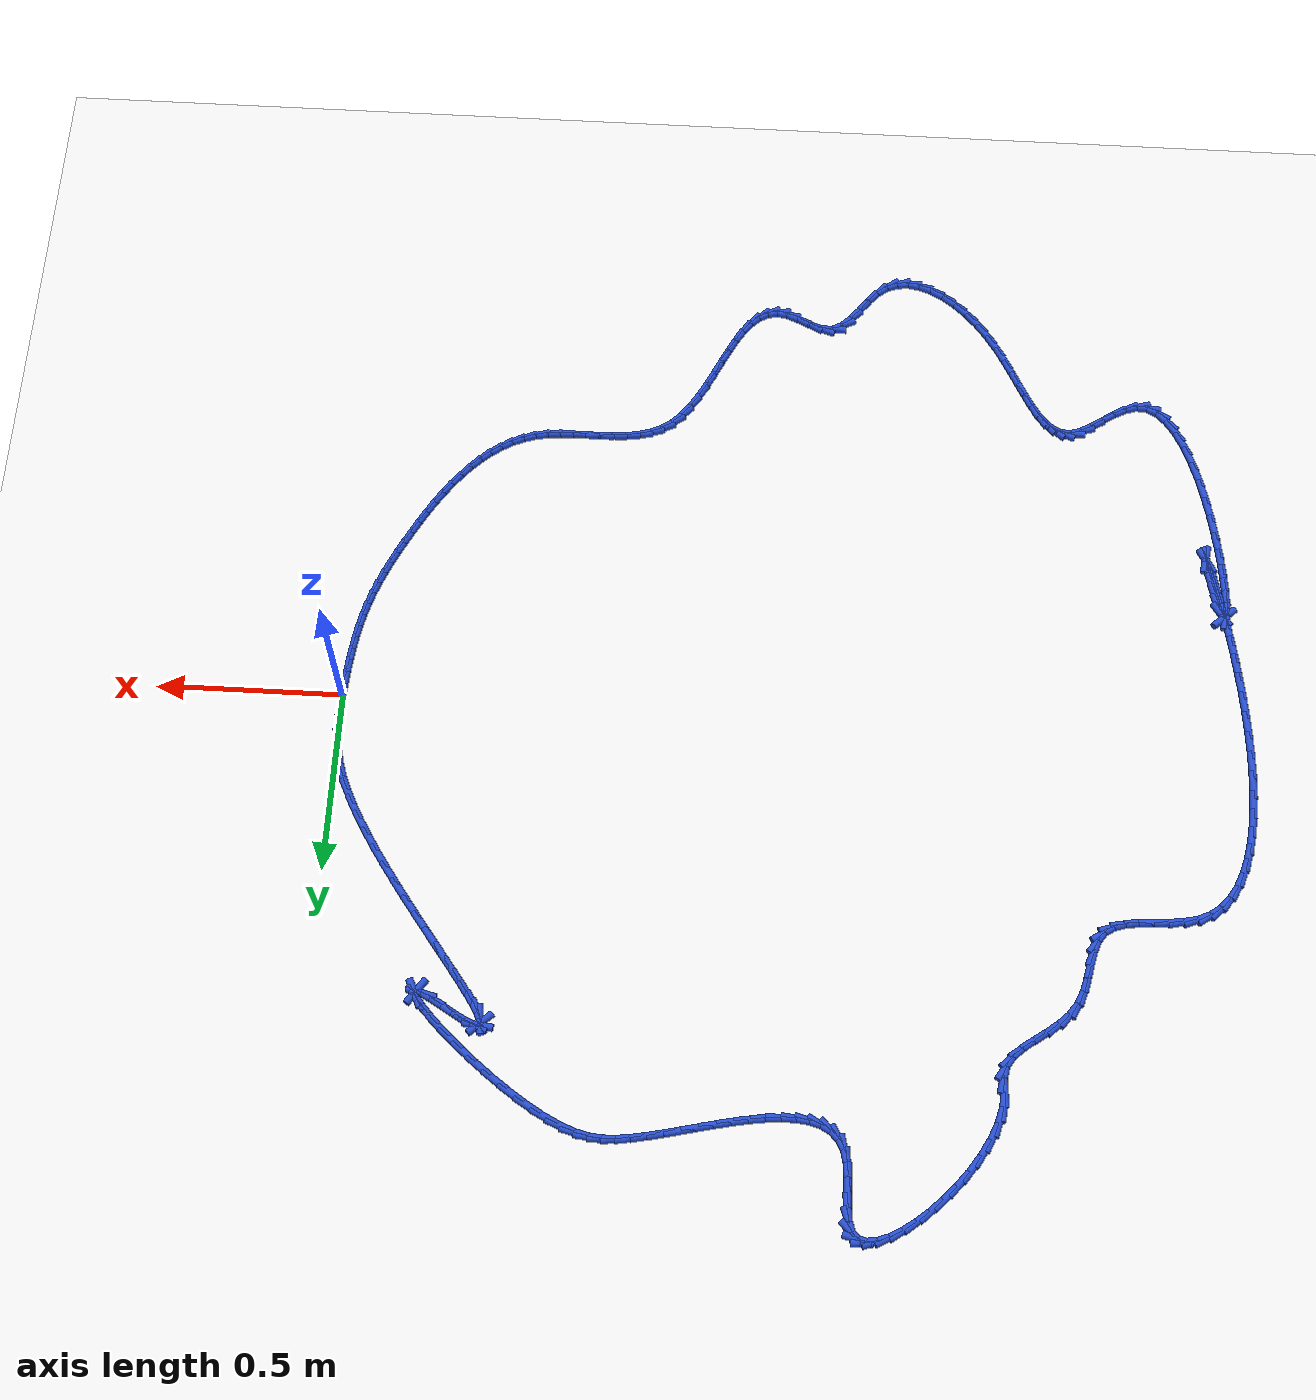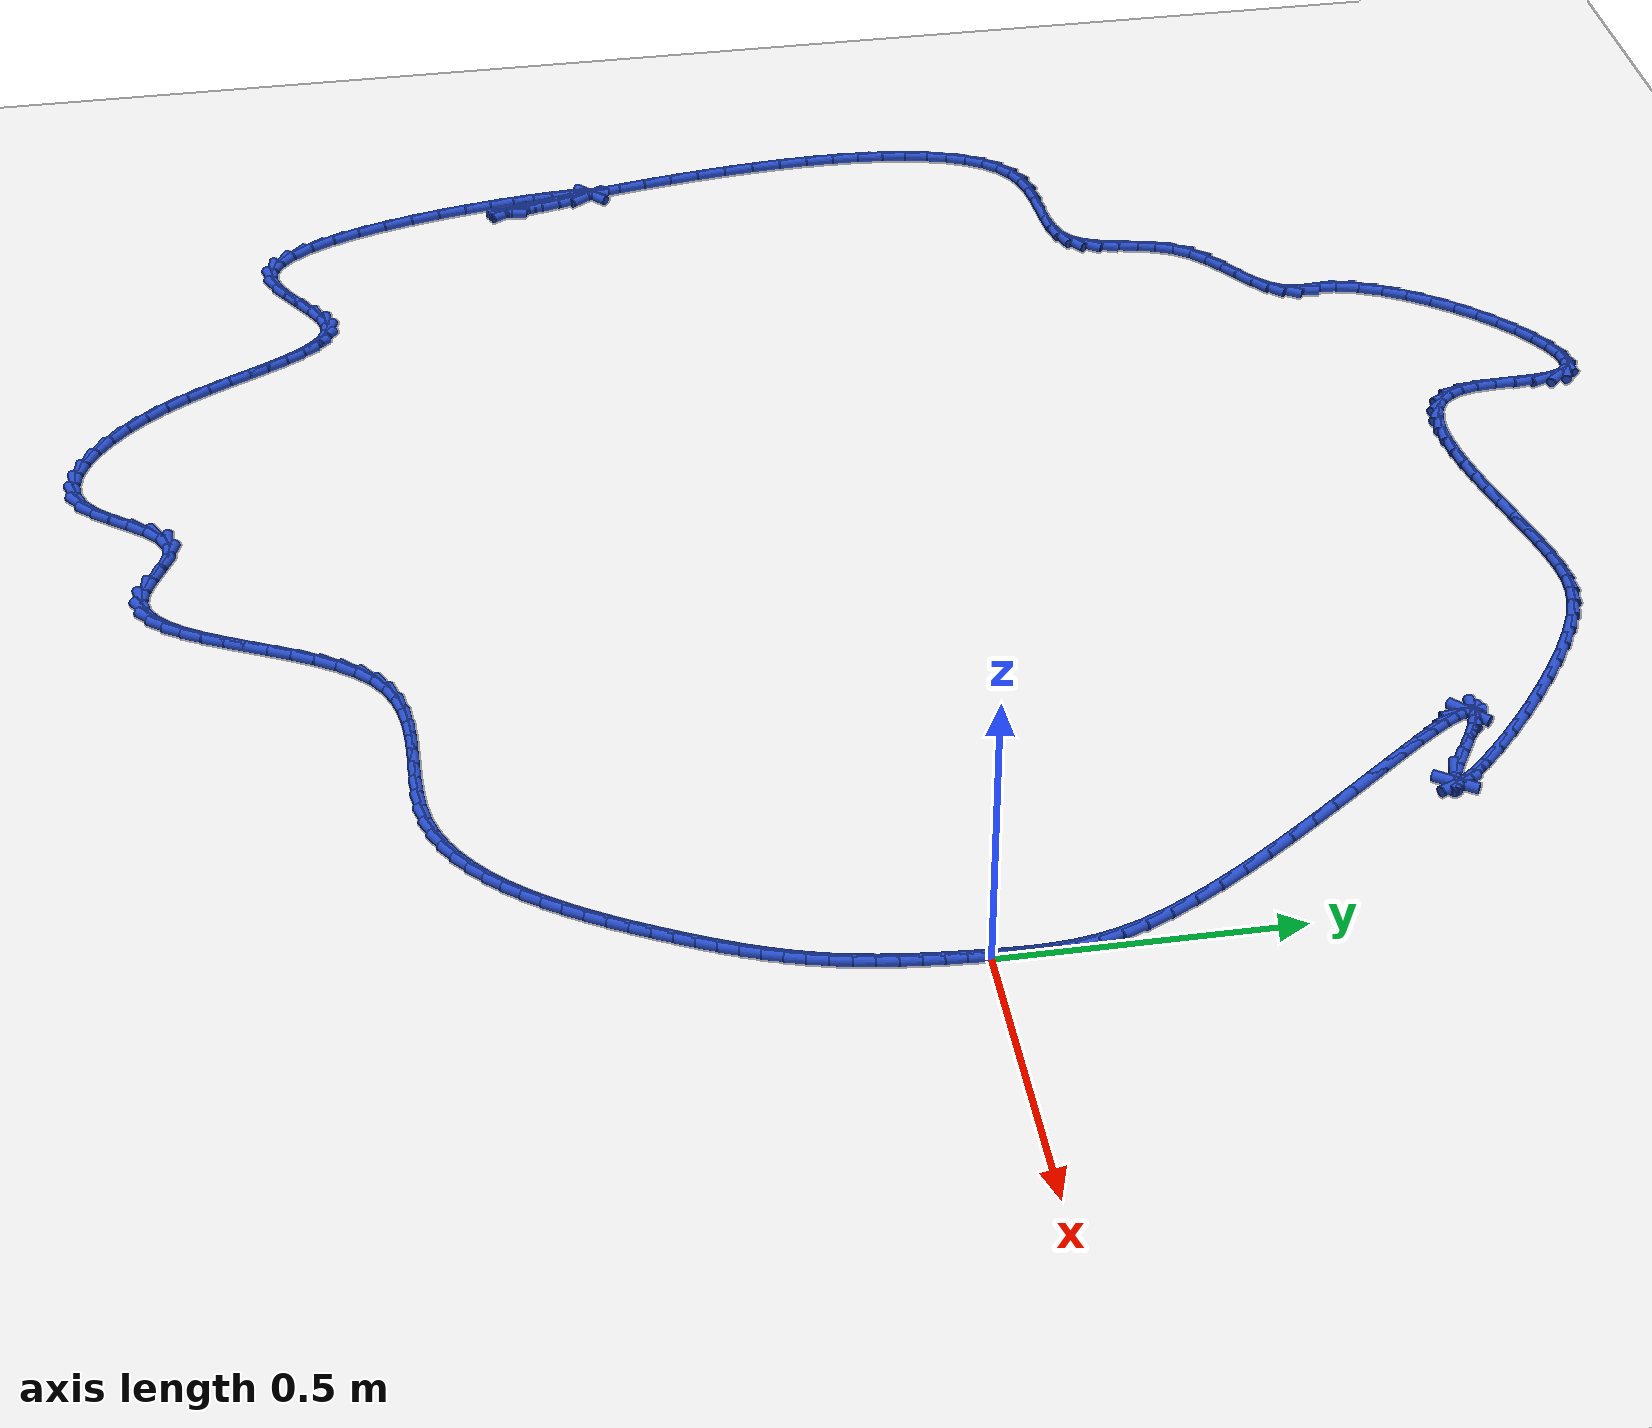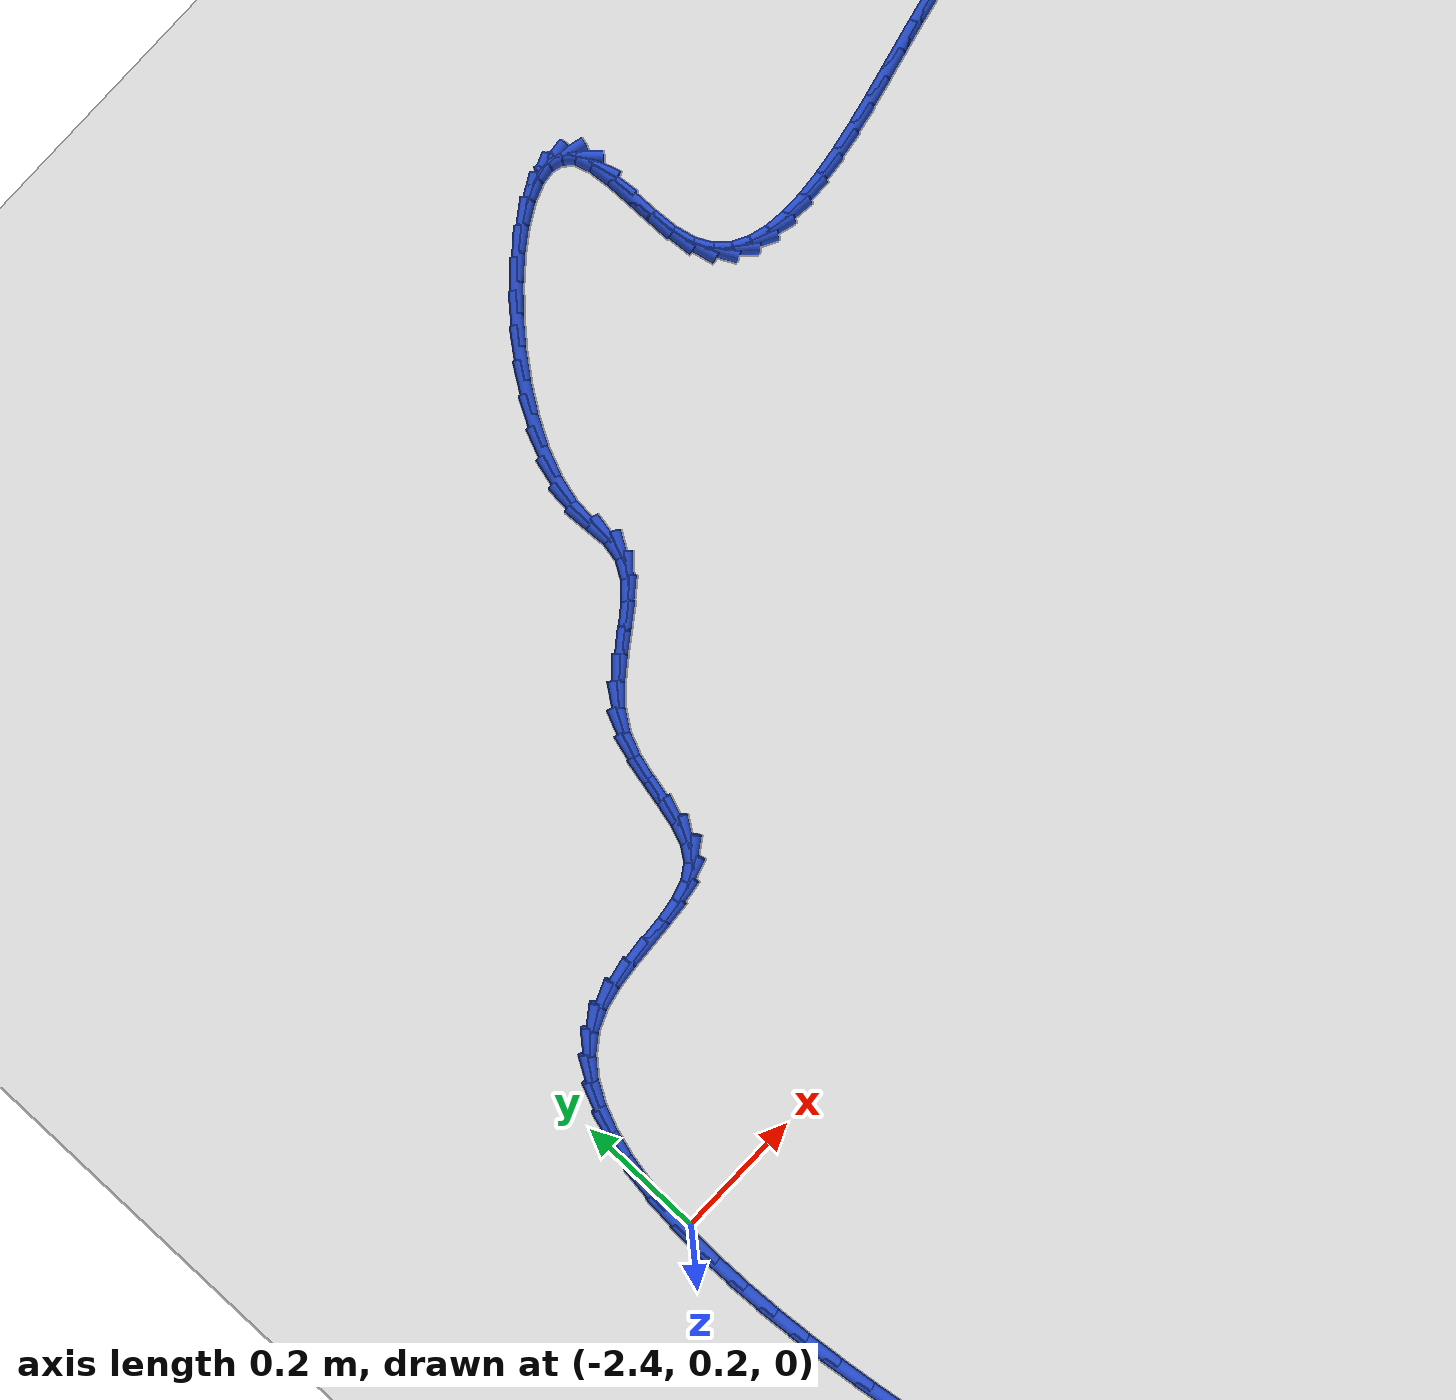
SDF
<sdf version="1.6">
 <world name="default">
  <light name="sun" type="directional">
   <pose>0 0 10 0 -0 0</pose>
   <diffuse>0.8 0.8 0.8 1</diffuse>
   <specular>0.2 0.2 0.2 1</specular>
   <attenuation>
    <range>1000</range>
    <constant>0.9</constant>
    <linear>0.01</linear>
    <quadratic>0.001</quadratic>
   </attenuation>
   <direction>-0.5 0.1 -0.9</direction>
  </light>
  <model name="ground_plane">
   <static>1</static>
   <link name="link">
    <collision name="collision">
     <geometry><plane><normal>0 0 1</normal><size>100 100</size></plane></geometry>
     <surface><friction><ode><mu>100</mu><mu2>50</mu2></ode></friction></surface>
    </collision>
    <visual name="visual">
     <cast_shadows>0</cast_shadows>
     <geometry><plane><normal>0 0 1</normal><size>100 100</size></plane></geometry>
     <material>
      <script><uri>file://media/materials/scripts/gazebo.material</uri><name>Gazebo/WhiteGlow</name></script>
     </material>
    </visual>
   </link>
  </model>
  <gravity>0 0 -9.8</gravity>
  <magnetic_field>6e-06 2.3e-05 -4.2e-05</magnetic_field>
  <atmosphere type="adiabatic"/>
  <physics name="default_physics" default="0" type="ode">
   <max_step_size>0.001</max_step_size>
   <real_time_factor>1</real_time_factor>
   <real_time_update_rate>1000</real_time_update_rate>
  </physics>
  <scene><ambient>0.4 0.4 0.4 1</ambient><background>0.7 0.7 0.7 1</background><shadows>1</shadows></scene>
  <spherical_coordinates>
   <surface_model>EARTH_WGS84</surface_model>
   <latitude_deg>0</latitude_deg>
   <longitude_deg>0</longitude_deg>
   <elevation>0</elevation>
   <heading_deg>0</heading_deg>
  </spherical_coordinates>
  <model name="line">
   <link name="link_0">
    <pose>8.673617379884035e-18 6.938893903907228e-18 0.01 0 1.57 1.523138118637967</pose>
    <collision name="collision">
     <geometry><cylinder><radius>0.01</radius><length>0.08</length></cylinder></geometry>
    </collision>
    <visual name="visual">
     <material>
      <script><name>Gazebo/Blue</name><uri>file://media/materials/scripts/gazebo.material</uri></script>
     </material>
     <geometry><cylinder><radius>0.01</radius><length>0.08</length></cylinder></geometry>
    </visual>
   </link>
   <link name="link_1">
    <pose>0.001585584483484348 0.03324472141092138 0.01 0 1.57 1.5499778389324392</pose>
    <collision name="collision">
     <geometry><cylinder><radius>0.01</radius><length>0.08</length></cylinder></geometry>
    </collision>
    <visual name="visual">
     <material>
      <script><name>Gazebo/Blue</name><uri>file://media/materials/scripts/gazebo.material</uri></script>
     </material>
     <geometry><cylinder><radius>0.01</radius><length>0.08</length></cylinder></geometry>
    </visual>
   </link>
   <link name="link_2">
    <pose>0.002270491347331482 0.06613894106540857 0.01 0 1.57 -1.5463468351426486</pose>
    <collision name="collision">
     <geometry><cylinder><radius>0.01</radius><length>0.08</length></cylinder></geometry>
    </collision>
    <visual name="visual">
     <material>
      <script><name>Gazebo/Blue</name><uri>file://media/materials/scripts/gazebo.material</uri></script>
     </material>
     <geometry><cylinder><radius>0.01</radius><length>0.08</length></cylinder></geometry>
    </visual>
   </link>
   <link name="link_3">
    <pose>0.0014635920974431383 0.09913506519120466 0.01 0 1.57 -1.4848743740156531</pose>
    <collision name="collision">
     <geometry><cylinder><radius>0.01</radius><length>0.08</length></cylinder></geometry>
    </collision>
    <visual name="visual">
     <material>
      <script><name>Gazebo/Blue</name><uri>file://media/materials/scripts/gazebo.material</uri></script>
     </material>
     <geometry><cylinder><radius>0.01</radius><length>0.08</length></cylinder></geometry>
    </visual>
   </link>
   <link name="link_4">
    <pose>-0.001426241760278957 0.13268550001605264 0.01 0 1.57 -1.4111606628722124</pose>
    <collision name="collision">
     <geometry><cylinder><radius>0.01</radius><length>0.08</length></cylinder></geometry>
    </collision>
    <visual name="visual">
     <material>
      <script><name>Gazebo/Blue</name><uri>file://media/materials/scripts/gazebo.material</uri></script>
     </material>
     <geometry><cylinder><radius>0.01</radius><length>0.08</length></cylinder></geometry>
    </visual>
   </link>
   <link name="link_5">
    <pose>-0.0069901387199330835 0.16724265176769548 0.01 0 1.57 -1.3303954426050388</pose>
    <collision name="collision">
     <geometry><cylinder><radius>0.01</radius><length>0.08</length></cylinder></geometry>
    </collision>
    <visual name="visual">
     <material>
      <script><name>Gazebo/Blue</name><uri>file://media/materials/scripts/gazebo.material</uri></script>
     </material>
     <geometry><cylinder><radius>0.01</radius><length>0.08</length></cylinder></geometry>
    </visual>
   </link>
   <link name="link_6">
    <pose>-0.01581922727561751 0.20325892667387624 0.01 0 1.57 -1.2480303315702033</pose>
    <collision name="collision">
     <geometry><cylinder><radius>0.01</radius><length>0.08</length></cylinder></geometry>
    </collision>
    <visual name="visual">
     <material>
      <script><name>Gazebo/Blue</name><uri>file://media/materials/scripts/gazebo.material</uri></script>
     </material>
     <geometry><cylinder><radius>0.01</radius><length>0.08</length></cylinder></geometry>
    </visual>
   </link>
   <link name="link_7">
    <pose>-0.028504635921430512 0.24118673096233786 0.01 0 1.57 -1.170263766637879</pose>
    <collision name="collision">
     <geometry><cylinder><radius>0.01</radius><length>0.08</length></cylinder></geometry>
    </collision>
    <visual name="visual">
     <material>
      <script><name>Gazebo/Blue</name><uri>file://media/materials/scripts/gazebo.material</uri></script>
     </material>
     <geometry><cylinder><radius>0.01</radius><length>0.08</length></cylinder></geometry>
    </visual>
   </link>
   <link name="link_8">
    <pose>-0.045530404801527875 0.28139674451726765 0.01 0 1.57 -1.108227529056862</pose>
    <collision name="collision">
     <geometry><cylinder><radius>0.01</radius><length>0.08</length></cylinder></geometry>
    </collision>
    <visual name="visual">
     <material>
      <script><name>Gazebo/Blue</name><uri>file://media/materials/scripts/gazebo.material</uri></script>
     </material>
     <geometry><cylinder><radius>0.01</radius><length>0.08</length></cylinder></geometry>
    </visual>
   </link>
   <link name="link_9">
    <pose>-0.0666113562889491 0.32367260525362546 0.01 0 1.57 -1.0612071020007114</pose>
    <collision name="collision">
     <geometry><cylinder><radius>0.01</radius><length>0.08</length></cylinder></geometry>
    </collision>
    <visual name="visual">
     <material>
      <script><name>Gazebo/Blue</name><uri>file://media/materials/scripts/gazebo.material</uri></script>
     </material>
     <geometry><cylinder><radius>0.01</radius><length>0.08</length></cylinder></geometry>
    </visual>
   </link>
   <link name="link_10">
    <pose>-0.09112605837543512 0.3675413326857432 0.01 0 1.57 -1.0249504982867321</pose>
    <collision name="collision">
     <geometry><cylinder><radius>0.01</radius><length>0.08</length></cylinder></geometry>
    </collision>
    <visual name="visual">
     <material>
      <script><name>Gazebo/Blue</name><uri>file://media/materials/scripts/gazebo.material</uri></script>
     </material>
     <geometry><cylinder><radius>0.01</radius><length>0.08</length></cylinder></geometry>
    </visual>
   </link>
   <link name="link_11">
    <pose>-0.11845166703816948 0.41252886872439537 0.01 0 1.57 -0.9966939153665987</pose>
    <collision name="collision">
     <geometry><cylinder><radius>0.01</radius><length>0.08</length></cylinder></geometry>
    </collision>
    <visual name="visual">
     <material>
      <script><name>Gazebo/Blue</name><uri>file://media/materials/scripts/gazebo.material</uri></script>
     </material>
     <geometry><cylinder><radius>0.01</radius><length>0.08</length></cylinder></geometry>
    </visual>
   </link>
   <link name="link_12">
    <pose>-0.14796533825433575 0.4581611552803567 0.01 0 1.57 -0.9746226463821942</pose>
    <collision name="collision">
     <geometry><cylinder><radius>0.01</radius><length>0.08</length></cylinder></geometry>
    </collision>
    <visual name="visual">
     <material>
      <script><name>Gazebo/Blue</name><uri>file://media/materials/scripts/gazebo.material</uri></script>
     </material>
     <geometry><cylinder><radius>0.01</radius><length>0.08</length></cylinder></geometry>
    </visual>
   </link>
   <link name="link_13">
    <pose>-0.1790442280011174 0.5039641342644017 0.01 0 1.57 -0.9575446194777869</pose>
    <collision name="collision">
     <geometry><cylinder><radius>0.01</radius><length>0.08</length></cylinder></geometry>
    </collision>
    <visual name="visual">
     <material>
      <script><name>Gazebo/Blue</name><uri>file://media/materials/scripts/gazebo.material</uri></script>
     </material>
     <geometry><cylinder><radius>0.01</radius><length>0.08</length></cylinder></geometry>
    </visual>
   </link>
   <link name="link_14">
    <pose>-0.21106549225569787 0.549463747587305 0.01 0 1.57 -0.9447026504581928</pose>
    <collision name="collision">
     <geometry><cylinder><radius>0.01</radius><length>0.08</length></cylinder></geometry>
    </collision>
    <visual name="visual">
     <material>
      <script><name>Gazebo/Blue</name><uri>file://media/materials/scripts/gazebo.material</uri></script>
     </material>
     <geometry><cylinder><radius>0.01</radius><length>0.08</length></cylinder></geometry>
    </visual>
   </link>
   <link name="link_15">
    <pose>-0.24340628699526076 0.5941859371598409 0.01 0 1.57 -0.935673681147409</pose>
    <collision name="collision">
     <geometry><cylinder><radius>0.01</radius><length>0.08</length></cylinder></geometry>
    </collision>
    <visual name="visual">
     <material>
      <script><name>Gazebo/Blue</name><uri>file://media/materials/scripts/gazebo.material</uri></script>
     </material>
     <geometry><cylinder><radius>0.01</radius><length>0.08</length></cylinder></geometry>
    </visual>
   </link>
   <link name="link_16">
    <pose>-0.2754437681969896 0.6376566448927845 0.01 0 1.57 -0.9303307999203727</pose>
    <collision name="collision">
     <geometry><cylinder><radius>0.01</radius><length>0.08</length></cylinder></geometry>
    </collision>
    <visual name="visual">
     <material>
      <script><name>Gazebo/Blue</name><uri>file://media/materials/scripts/gazebo.material</uri></script>
     </material>
     <geometry><cylinder><radius>0.01</radius><length>0.08</length></cylinder></geometry>
    </visual>
   </link>
   <link name="link_17">
    <pose>-0.30655509183806806 0.6794018126969104 0.01 0 1.57 -0.928864554065546</pose>
    <collision name="collision">
     <geometry><cylinder><radius>0.01</radius><length>0.08</length></cylinder></geometry>
    </collision>
    <visual name="visual">
     <material>
      <script><name>Gazebo/Blue</name><uri>file://media/materials/scripts/gazebo.material</uri></script>
     </material>
     <geometry><cylinder><radius>0.01</radius><length>0.08</length></cylinder></geometry>
    </visual>
   </link>
   <link name="link_18">
    <pose>-0.33611741389567934 0.7189473824829925 0.01 0 1.57 -0.9318838796647777</pose>
    <collision name="collision">
     <geometry><cylinder><radius>0.01</radius><length>0.08</length></cylinder></geometry>
    </collision>
    <visual name="visual">
     <material>
      <script><name>Gazebo/Blue</name><uri>file://media/materials/scripts/gazebo.material</uri></script>
     </material>
     <geometry><cylinder><radius>0.01</radius><length>0.08</length></cylinder></geometry>
    </visual>
   </link>
   <link name="link_19">
    <pose>-0.3635078903470071 0.7558192961618062 0.01 0 1.57 -0.9406612782921225</pose>
    <collision name="collision">
     <geometry><cylinder><radius>0.01</radius><length>0.08</length></cylinder></geometry>
    </collision>
    <visual name="visual">
     <material>
      <script><name>Gazebo/Blue</name><uri>file://media/materials/scripts/gazebo.material</uri></script>
     </material>
     <geometry><cylinder><radius>0.01</radius><length>0.08</length></cylinder></geometry>
    </visual>
   </link>
   <link name="link_20">
    <pose>-0.3881036771692349 0.7895434956441257 0.01 0 1.57 -0.9576986605762746</pose>
    <collision name="collision">
     <geometry><cylinder><radius>0.01</radius><length>0.08</length></cylinder></geometry>
    </collision>
    <visual name="visual">
     <material>
      <script><name>Gazebo/Blue</name><uri>file://media/materials/scripts/gazebo.material</uri></script>
     </material>
     <geometry><cylinder><radius>0.01</radius><length>0.08</length></cylinder></geometry>
    </visual>
   </link>
   <link name="link_21">
    <pose>-0.4092819303395462 0.8196459228407256 0.01 0 1.57 -0.9881328618419942</pose>
    <collision name="collision">
     <geometry><cylinder><radius>0.01</radius><length>0.08</length></cylinder></geometry>
    </collision>
    <visual name="visual">
     <material>
      <script><name>Gazebo/Blue</name><uri>file://media/materials/scripts/gazebo.material</uri></script>
     </material>
     <geometry><cylinder><radius>0.01</radius><length>0.08</length></cylinder></geometry>
    </visual>
   </link>
   <link name="link_22">
    <pose>-0.4264198058351244 0.8456525196623805 0.01 0 1.57 -1.043769909391207</pose>
    <collision name="collision">
     <geometry><cylinder><radius>0.01</radius><length>0.08</length></cylinder></geometry>
    </collision>
    <visual name="visual">
     <material>
      <script><name>Gazebo/Blue</name><uri>file://media/materials/scripts/gazebo.material</uri></script>
     </material>
     <geometry><cylinder><radius>0.01</radius><length>0.08</length></cylinder></geometry>
    </visual>
   </link>
   <link name="link_23">
    <pose>-0.4388944596331535 0.8670892280198653 0.01 0 1.57 -1.1575283264766851</pose>
    <collision name="collision">
     <geometry><cylinder><radius>0.01</radius><length>0.08</length></cylinder></geometry>
    </collision>
    <visual name="visual">
     <material>
      <script><name>Gazebo/Blue</name><uri>file://media/materials/scripts/gazebo.material</uri></script>
     </material>
     <geometry><cylinder><radius>0.01</radius><length>0.08</length></cylinder></geometry>
    </visual>
   </link>
   <link name="link_24">
    <pose>-0.44608304771081664 0.8834819898239545 0.01 0 1.57 -1.4536608129962254</pose>
    <collision name="collision">
     <geometry><cylinder><radius>0.01</radius><length>0.08</length></cylinder></geometry>
    </collision>
    <visual name="visual">
     <material>
      <script><name>Gazebo/Blue</name><uri>file://media/materials/scripts/gazebo.material</uri></script>
     </material>
     <geometry><cylinder><radius>0.01</radius><length>0.08</length></cylinder></geometry>
    </visual>
   </link>
   <link name="link_25">
    <pose>-0.44736272604529714 0.8943567469854222 0.01 0 1.57 0.7489673832095932</pose>
    <collision name="collision">
     <geometry><cylinder><radius>0.01</radius><length>0.08</length></cylinder></geometry>
    </collision>
    <visual name="visual">
     <material>
      <script><name>Gazebo/Blue</name><uri>file://media/materials/scripts/gazebo.material</uri></script>
     </material>
     <geometry><cylinder><radius>0.01</radius><length>0.08</length></cylinder></geometry>
    </visual>
   </link>
   <link name="link_26">
    <pose>-0.44211065061377897 0.8992394414150439 0.01 0 1.57 -0.12694073009909124</pose>
    <collision name="collision">
     <geometry><cylinder><radius>0.01</radius><length>0.08</length></cylinder></geometry>
    </collision>
    <visual name="visual">
     <material>
      <script><name>Gazebo/Blue</name><uri>file://media/materials/scripts/gazebo.material</uri></script>
     </material>
     <geometry><cylinder><radius>0.01</radius><length>0.08</length></cylinder></geometry>
    </visual>
   </link>
   <link name="link_27">
    <pose>-0.42970397739344535 0.8976560150235933 0.01 0 1.57 -0.3995753435187933</pose>
    <collision name="collision">
     <geometry><cylinder><radius>0.01</radius><length>0.08</length></cylinder></geometry>
    </collision>
    <visual name="visual">
     <material>
      <script><name>Gazebo/Blue</name><uri>file://media/materials/scripts/gazebo.material</uri></script>
     </material>
     <geometry><cylinder><radius>0.01</radius><length>0.08</length></cylinder></geometry>
    </visual>
   </link>
   <link name="link_28">
    <pose>-0.40951986236147986 0.8891324097218452 0.01 0 1.57 -0.5057709338530939</pose>
    <collision name="collision">
     <geometry><cylinder><radius>0.01</radius><length>0.08</length></cylinder></geometry>
    </collision>
    <visual name="visual">
     <material>
      <script><name>Gazebo/Blue</name><uri>file://media/materials/scripts/gazebo.material</uri></script>
     </material>
     <geometry><cylinder><radius>0.01</radius><length>0.08</length></cylinder></geometry>
    </visual>
   </link>
   <link name="link_29">
    <pose>-0.3812875806829965 0.8734968210229603 0.01 0 1.57 -0.5407796485388793</pose>
    <collision name="collision">
     <geometry><cylinder><radius>0.01</radius><length>0.08</length></cylinder></geometry>
    </collision>
    <visual name="visual">
     <material>
      <script><name>Gazebo/Blue</name><uri>file://media/materials/scripts/gazebo.material</uri></script>
     </material>
     <geometry><cylinder><radius>0.01</radius><length>0.08</length></cylinder></geometry>
    </visual>
   </link>
   <link name="link_30">
    <pose>-0.34850060639415553 0.8538085738640765 0.01 0 1.57 -0.5353574790282457</pose>
    <collision name="collision">
     <geometry><cylinder><radius>0.01</radius><length>0.08</length></cylinder></geometry>
    </collision>
    <visual name="visual">
     <material>
      <script><name>Gazebo/Blue</name><uri>file://media/materials/scripts/gazebo.material</uri></script>
     </material>
     <geometry><cylinder><radius>0.01</radius><length>0.08</length></cylinder></geometry>
    </visual>
   </link>
   <link name="link_31">
    <pose>-0.3169332386560779 0.8350848177884911 0.01 0 1.57 -0.4781612451844935</pose>
    <collision name="collision">
     <geometry><cylinder><radius>0.01</radius><length>0.08</length></cylinder></geometry>
    </collision>
    <visual name="visual">
     <material>
      <script><name>Gazebo/Blue</name><uri>file://media/materials/scripts/gazebo.material</uri></script>
     </material>
     <geometry><cylinder><radius>0.01</radius><length>0.08</length></cylinder></geometry>
    </visual>
   </link>
   <link name="link_32">
    <pose>-0.2923798101428956 0.8223593662075089 0.01 0 1.57 -0.24977682648921742</pose>
    <collision name="collision">
     <geometry><cylinder><radius>0.01</radius><length>0.08</length></cylinder></geometry>
    </collision>
    <visual name="visual">
     <material>
      <script><name>Gazebo/Blue</name><uri>file://media/materials/scripts/gazebo.material</uri></script>
     </material>
     <geometry><cylinder><radius>0.01</radius><length>0.08</length></cylinder></geometry>
    </visual>
   </link>
   <link name="link_33">
    <pose>-0.2786245325676537 0.8188503369821315 0.01 0 1.57 0.9764913637129256</pose>
    <collision name="collision">
     <geometry><cylinder><radius>0.01</radius><length>0.08</length></cylinder></geometry>
    </collision>
    <visual name="visual">
     <material>
      <script><name>Gazebo/Blue</name><uri>file://media/materials/scripts/gazebo.material</uri></script>
     </material>
     <geometry><cylinder><radius>0.01</radius><length>0.08</length></cylinder></geometry>
    </visual>
   </link>
   <link name="link_34">
    <pose>-0.2751925252135136 0.8239287087598621 0.01 0 1.57 -1.132956064692277</pose>
    <collision name="collision">
     <geometry><cylinder><radius>0.01</radius><length>0.08</length></cylinder></geometry>
    </collision>
    <visual name="visual">
     <material>
      <script><name>Gazebo/Blue</name><uri>file://media/materials/scripts/gazebo.material</uri></script>
     </material>
     <geometry><cylinder><radius>0.01</radius><length>0.08</length></cylinder></geometry>
    </visual>
   </link>
   <link name="link_35">
    <pose>-0.2810660630108827 0.8364751214996956 0.01 0 1.57 -0.9276327409792565</pose>
    <collision name="collision">
     <geometry><cylinder><radius>0.01</radius><length>0.08</length></cylinder></geometry>
    </collision>
    <visual name="visual">
     <material>
      <script><name>Gazebo/Blue</name><uri>file://media/materials/scripts/gazebo.material</uri></script>
     </material>
     <geometry><cylinder><radius>0.01</radius><length>0.08</length></cylinder></geometry>
    </visual>
   </link>
   <link name="link_36">
    <pose>-0.2952274208901677 0.855370215160626 0.01 0 1.57 -0.8444428398833422</pose>
    <collision name="collision">
     <geometry><cylinder><radius>0.01</radius><length>0.08</length></cylinder></geometry>
    </collision>
    <visual name="visual">
     <material>
      <script><name>Gazebo/Blue</name><uri>file://media/materials/scripts/gazebo.material</uri></script>
     </material>
     <geometry><cylinder><radius>0.01</radius><length>0.08</length></cylinder></geometry>
    </visual>
   </link>
   <link name="link_37">
    <pose>-0.3166588737817755 0.8794946297016479 0.01 0 1.57 -0.7952435227738177</pose>
    <collision name="collision">
     <geometry><cylinder><radius>0.01</radius><length>0.08</length></cylinder></geometry>
    </collision>
    <visual name="visual">
     <material>
      <script><name>Gazebo/Blue</name><uri>file://media/materials/scripts/gazebo.material</uri></script>
     </material>
     <geometry><cylinder><radius>0.01</radius><length>0.08</length></cylinder></geometry>
    </visual>
   </link>
   <link name="link_38">
    <pose>-0.3443426966161134 0.9077290050817559 0.01 0 1.57 -0.7590026643309477</pose>
    <collision name="collision">
     <geometry><cylinder><radius>0.01</radius><length>0.08</length></cylinder></geometry>
    </collision>
    <visual name="visual">
     <material>
      <script><name>Gazebo/Blue</name><uri>file://media/materials/scripts/gazebo.material</uri></script>
     </material>
     <geometry><cylinder><radius>0.01</radius><length>0.08</length></cylinder></geometry>
    </visual>
   </link>
   <link name="link_39">
    <pose>-0.3772611643235882 0.9389539812599442 0.01 0 1.57 -0.7279492977358222</pose>
    <collision name="collision">
     <geometry><cylinder><radius>0.01</radius><length>0.08</length></cylinder></geometry>
    </collision>
    <visual name="visual">
     <material>
      <script><name>Gazebo/Blue</name><uri>file://media/materials/scripts/gazebo.material</uri></script>
     </material>
     <geometry><cylinder><radius>0.01</radius><length>0.08</length></cylinder></geometry>
    </visual>
   </link>
   <link name="link_40">
    <pose>-0.414396551834607 0.9720501981952072 0.01 0 1.57 -0.6981806495435944</pose>
    <collision name="collision">
     <geometry><cylinder><radius>0.01</radius><length>0.08</length></cylinder></geometry>
    </collision>
    <visual name="visual">
     <material>
      <script><name>Gazebo/Blue</name><uri>file://media/materials/scripts/gazebo.material</uri></script>
     </material>
     <geometry><cylinder><radius>0.01</radius><length>0.08</length></cylinder></geometry>
    </visual>
   </link>
   <link name="link_41">
    <pose>-0.45473113407957666 1.0058982958465397 0.01 0 1.57 -0.6670611653092716</pose>
    <collision name="collision">
     <geometry><cylinder><radius>0.01</radius><length>0.08</length></cylinder></geometry>
    </collision>
    <visual name="visual">
     <material>
      <script><name>Gazebo/Blue</name><uri>file://media/materials/scripts/gazebo.material</uri></script>
     </material>
     <geometry><cylinder><radius>0.01</radius><length>0.08</length></cylinder></geometry>
    </visual>
   </link>
   <link name="link_42">
    <pose>-0.4972471859889044 1.039378914172936 0.01 0 1.57 -0.6321818000430323</pose>
    <collision name="collision">
     <geometry><cylinder><radius>0.01</radius><length>0.08</length></cylinder></geometry>
    </collision>
    <visual name="visual">
     <material>
      <script><name>Gazebo/Blue</name><uri>file://media/materials/scripts/gazebo.material</uri></script>
     </material>
     <geometry><cylinder><radius>0.01</radius><length>0.08</length></cylinder></geometry>
    </visual>
   </link>
   <link name="link_43">
    <pose>-0.540926982492997 1.07137269313339 0.01 0 1.57 -0.5906890601484294</pose>
    <collision name="collision">
     <geometry><cylinder><radius>0.01</radius><length>0.08</length></cylinder></geometry>
    </collision>
    <visual name="visual">
     <material>
      <script><name>Gazebo/Blue</name><uri>file://media/materials/scripts/gazebo.material</uri></script>
     </material>
     <geometry><cylinder><radius>0.01</radius><length>0.08</length></cylinder></geometry>
    </visual>
   </link>
   <link name="link_44">
    <pose>-0.5847527985222611 1.1007602726868964 0.01 0 1.57 -0.5385267230611902</pose>
    <collision name="collision">
     <geometry><cylinder><radius>0.01</radius><length>0.08</length></cylinder></geometry>
    </collision>
    <visual name="visual">
     <material>
      <script><name>Gazebo/Blue</name><uri>file://media/materials/scripts/gazebo.material</uri></script>
     </material>
     <geometry><cylinder><radius>0.01</radius><length>0.08</length></cylinder></geometry>
    </visual>
   </link>
   <link name="link_45">
    <pose>-0.6277069090071045 1.12642229279245 0.01 0 1.57 -0.4691797618339758</pose>
    <collision name="collision">
     <geometry><cylinder><radius>0.01</radius><length>0.08</length></cylinder></geometry>
    </collision>
    <visual name="visual">
     <material>
      <script><name>Gazebo/Blue</name><uri>file://media/materials/scripts/gazebo.material</uri></script>
     </material>
     <geometry><cylinder><radius>0.01</radius><length>0.08</length></cylinder></geometry>
    </visual>
   </link>
   <link name="link_46">
    <pose>-0.6687715888779338 1.147239393409045 0.01 0 1.57 -0.3714641257997168</pose>
    <collision name="collision">
     <geometry><cylinder><radius>0.01</radius><length>0.08</length></cylinder></geometry>
    </collision>
    <visual name="visual">
     <material>
      <script><name>Gazebo/Blue</name><uri>file://media/materials/scripts/gazebo.material</uri></script>
     </material>
     <geometry><cylinder><radius>0.01</radius><length>0.08</length></cylinder></geometry>
    </visual>
   </link>
   <link name="link_47">
    <pose>-0.7069542159719195 1.162113378735111 0.01 0 1.57 -0.24112769476727797</pose>
    <collision name="collision">
     <geometry><cylinder><radius>0.01</radius><length>0.08</length></cylinder></geometry>
    </collision>
    <visual name="visual">
     <material>
      <script><name>Gazebo/Blue</name><uri>file://media/materials/scripts/gazebo.material</uri></script>
     </material>
     <geometry><cylinder><radius>0.01</radius><length>0.08</length></cylinder></geometry>
    </visual>
   </link>
   <link name="link_48">
    <pose>-0.7422736971313185 1.1707988722166913 0.01 0 1.57 -0.09955596365791529</pose>
    <collision name="collision">
     <geometry><cylinder><radius>0.01</radius><length>0.08</length></cylinder></geometry>
    </collision>
    <visual name="visual">
     <material>
      <script><name>Gazebo/Blue</name><uri>file://media/materials/scripts/gazebo.material</uri></script>
     </material>
     <geometry><cylinder><radius>0.01</radius><length>0.08</length></cylinder></geometry>
    </visual>
   </link>
   <link name="link_49">
    <pose>-0.7760839575784624 1.1741760501655636 0.01 0 1.57 0.028852323744959447</pose>
    <collision name="collision">
     <geometry><cylinder><radius>0.01</radius><length>0.08</length></cylinder></geometry>
    </collision>
    <visual name="visual">
     <material>
      <script><name>Gazebo/Blue</name><uri>file://media/materials/scripts/gazebo.material</uri></script>
     </material>
     <geometry><cylinder><radius>0.01</radius><length>0.08</length></cylinder></geometry>
    </visual>
   </link>
   <link name="link_50">
    <pose>-0.8098302889282178 1.1732021198216802 0.01 0 1.57 0.12370660788881764</pose>
    <collision name="collision">
     <geometry><cylinder><radius>0.01</radius><length>0.08</length></cylinder></geometry>
    </collision>
    <visual name="visual">
     <material>
      <script><name>Gazebo/Blue</name><uri>file://media/materials/scripts/gazebo.material</uri></script>
     </material>
     <geometry><cylinder><radius>0.01</radius><length>0.08</length></cylinder></geometry>
    </visual>
   </link>
   <link name="link_51">
    <pose>-0.8449579827954521 1.1688342884249954 0.01 0 1.57 0.17986273192217148</pose>
    <collision name="collision">
     <geometry><cylinder><radius>0.01</radius><length>0.08</length></cylinder></geometry>
    </collision>
    <visual name="visual">
     <material>
      <script><name>Gazebo/Blue</name><uri>file://media/materials/scripts/gazebo.material</uri></script>
     </material>
     <geometry><cylinder><radius>0.01</radius><length>0.08</length></cylinder></geometry>
    </visual>
   </link>
   <link name="link_52">
    <pose>-0.8826260631650705 1.1619851872863178 0.01 0 1.57 0.21252568031824093</pose>
    <collision name="collision">
     <geometry><cylinder><radius>0.01</radius><length>0.08</length></cylinder></geometry>
    </collision>
    <visual name="visual">
     <material>
      <script><name>Gazebo/Blue</name><uri>file://media/materials/scripts/gazebo.material</uri></script>
     </material>
     <geometry><cylinder><radius>0.01</radius><length>0.08</length></cylinder></geometry>
    </visual>
   </link>
   <link name="link_53">
    <pose>-0.9226241938450315 1.153354218919929 0.01 0 1.57 0.2302559881334819</pose>
    <collision name="collision">
     <geometry><cylinder><radius>0.01</radius><length>0.08</length></cylinder></geometry>
    </collision>
    <visual name="visual">
     <material>
      <script><name>Gazebo/Blue</name><uri>file://media/materials/scripts/gazebo.material</uri></script>
     </material>
     <geometry><cylinder><radius>0.01</radius><length>0.08</length></cylinder></geometry>
    </visual>
   </link>
   <link name="link_54">
    <pose>-0.9643330592238658 1.1435771019453427 0.01 0 1.57 0.23588753970900553</pose>
    <collision name="collision">
     <geometry><cylinder><radius>0.01</radius><length>0.08</length></cylinder></geometry>
    </collision>
    <visual name="visual">
     <material>
      <script><name>Gazebo/Blue</name><uri>file://media/materials/scripts/gazebo.material</uri></script>
     </material>
     <geometry><cylinder><radius>0.01</radius><length>0.08</length></cylinder></geometry>
    </visual>
   </link>
   <link name="link_55">
    <pose>-1.0071332711896268 1.1332895436927193 0.01 0 1.57 0.23066592869244337</pose>
    <collision name="collision">
     <geometry><cylinder><radius>0.01</radius><length>0.08</length></cylinder></geometry>
    </collision>
    <visual name="visual">
     <material>
      <script><name>Gazebo/Blue</name><uri>file://media/materials/scripts/gazebo.material</uri></script>
     </material>
     <geometry><cylinder><radius>0.01</radius><length>0.08</length></cylinder></geometry>
    </visual>
   </link>
   <link name="link_56">
    <pose>-1.0504054416303683 1.1231272514922208 0.01 0 1.57 0.2146446117185</pose>
    <collision name="collision">
     <geometry><cylinder><radius>0.01</radius><length>0.08</length></cylinder></geometry>
    </collision>
    <visual name="visual">
     <material>
      <script><name>Gazebo/Blue</name><uri>file://media/materials/scripts/gazebo.material</uri></script>
     </material>
     <geometry><cylinder><radius>0.01</radius><length>0.08</length></cylinder></geometry>
    </visual>
   </link>
   <link name="link_57">
    <pose>-1.093530182434144 1.1137259326740079 0.01 0 1.57 0.1867736046197251</pose>
    <collision name="collision">
     <geometry><cylinder><radius>0.01</radius><length>0.08</length></cylinder></geometry>
    </collision>
    <visual name="visual">
     <material>
      <script><name>Gazebo/Blue</name><uri>file://media/materials/scripts/gazebo.material</uri></script>
     </material>
     <geometry><cylinder><radius>0.01</radius><length>0.08</length></cylinder></geometry>
    </visual>
   </link>
   <link name="link_58">
    <pose>-1.1358881054890078 1.105721294568242 0.01 0 1.57 0.14474577143568657</pose>
    <collision name="collision">
     <geometry><cylinder><radius>0.01</radius><length>0.08</length></cylinder></geometry>
    </collision>
    <visual name="visual">
     <material>
      <script><name>Gazebo/Blue</name><uri>file://media/materials/scripts/gazebo.material</uri></script>
     </material>
     <geometry><cylinder><radius>0.01</radius><length>0.08</length></cylinder></geometry>
    </visual>
   </link>
   <link name="link_59">
    <pose>-1.1768598226830136 1.0997490445050842 0.01 0 1.57 0.08459320899463034</pose>
    <collision name="collision">
     <geometry><cylinder><radius>0.01</radius><length>0.08</length></cylinder></geometry>
    </collision>
    <visual name="visual">
     <material>
      <script><name>Gazebo/Blue</name><uri>file://media/materials/scripts/gazebo.material</uri></script>
     </material>
     <geometry><cylinder><radius>0.01</radius><length>0.08</length></cylinder></geometry>
    </visual>
   </link>
   <link name="link_60">
    <pose>-1.2158259459042147 1.0964448898146952 0.01 0 1.57 9.685646825418196e-06</pose>
    <collision name="collision">
     <geometry><cylinder><radius>0.01</radius><length>0.08</length></cylinder></geometry>
    </collision>
    <visual name="visual">
     <material>
      <script><name>Gazebo/Blue</name><uri>file://media/materials/scripts/gazebo.material</uri></script>
     </material>
     <geometry><cylinder><radius>0.01</radius><length>0.08</length></cylinder></geometry>
    </visual>
   </link>
   <link name="link_61">
    <pose>-1.2521670870406656 1.096444537827237 0.01 0 1.57 -0.11846214110581711</pose>
    <collision name="collision">
     <geometry><cylinder><radius>0.01</radius><length>0.08</length></cylinder></geometry>
    </collision>
    <visual name="visual">
     <material>
      <script><name>Gazebo/Blue</name><uri>file://media/materials/scripts/gazebo.material</uri></script>
     </material>
     <geometry><cylinder><radius>0.01</radius><length>0.08</length></cylinder></geometry>
    </visual>
   </link>
   <link name="link_62">
    <pose>-1.28526385798042 1.1003836958728703 0.01 0 1.57 -0.28341827992853147</pose>
    <collision name="collision">
     <geometry><cylinder><radius>0.01</radius><length>0.08</length></cylinder></geometry>
    </collision>
    <visual name="visual">
     <material>
      <script><name>Gazebo/Blue</name><uri>file://media/materials/scripts/gazebo.material</uri></script>
     </material>
     <geometry><cylinder><radius>0.01</radius><length>0.08</length></cylinder></geometry>
    </visual>
   </link>
   <link name="link_63">
    <pose>-1.3144968706115312 1.1088980712817562 0.01 0 1.57 -0.506337869939438</pose>
    <collision name="collision">
     <geometry><cylinder><radius>0.01</radius><length>0.08</length></cylinder></geometry>
    </collision>
    <visual name="visual">
     <material>
      <script><name>Gazebo/Blue</name><uri>file://media/materials/scripts/gazebo.material</uri></script>
     </material>
     <geometry><cylinder><radius>0.01</radius><length>0.08</length></cylinder></geometry>
    </visual>
   </link>
   <link name="link_64">
    <pose>-1.3392467368220535 1.122623371384056 0.01 0 1.57 -0.7834756525722651</pose>
    <collision name="collision">
     <geometry><cylinder><radius>0.01</radius><length>0.08</length></cylinder></geometry>
    </collision>
    <visual name="visual">
     <material>
      <script><name>Gazebo/Blue</name><uri>file://media/materials/scripts/gazebo.material</uri></script>
     </material>
     <geometry><cylinder><radius>0.01</radius><length>0.08</length></cylinder></geometry>
    </visual>
   </link>
   <link name="link_65">
    <pose>-1.3588940685000401 1.1421953035099306 0.01 0 1.57 -1.0799490202316058</pose>
    <collision name="collision">
     <geometry><cylinder><radius>0.01</radius><length>0.08</length></cylinder></geometry>
    </collision>
    <visual name="visual">
     <material>
      <script><name>Gazebo/Blue</name><uri>file://media/materials/scripts/gazebo.material</uri></script>
     </material>
     <geometry><cylinder><radius>0.01</radius><length>0.08</length></cylinder></geometry>
    </visual>
   </link>
   <link name="link_66">
    <pose>-1.3728194775335463 1.168249574989542 0.01 0 1.57 -1.336588557436155</pose>
    <collision name="collision">
     <geometry><cylinder><radius>0.01</radius><length>0.08</length></cylinder></geometry>
    </collision>
    <visual name="visual">
     <material>
      <script><name>Gazebo/Blue</name><uri>file://media/materials/scripts/gazebo.material</uri></script>
     </material>
     <geometry><cylinder><radius>0.01</radius><length>0.08</length></cylinder></geometry>
    </visual>
   </link>
   <link name="link_67">
    <pose>-1.380657377126296 1.2011010098026282 0.01 0 1.57 -1.484229218032587</pose>
    <collision name="collision">
     <geometry><cylinder><radius>0.01</radius><length>0.08</length></cylinder></geometry>
    </collision>
    <visual name="visual">
     <material>
      <script><name>Gazebo/Blue</name><uri>file://media/materials/scripts/gazebo.material</uri></script>
     </material>
     <geometry><cylinder><radius>0.01</radius><length>0.08</length></cylinder></geometry>
    </visual>
   </link>
   <link name="link_68">
    <pose>-1.3839195719427344 1.2386908285440446 0.01 0 1.57 -1.5442652184948247</pose>
    <collision name="collision">
     <geometry><cylinder><radius>0.01</radius><length>0.08</length></cylinder></geometry>
    </collision>
    <visual name="visual">
     <material>
      <script><name>Gazebo/Blue</name><uri>file://media/materials/scripts/gazebo.material</uri></script>
     </material>
     <geometry><cylinder><radius>0.01</radius><length>0.08</length></cylinder></geometry>
    </visual>
   </link>
   <link name="link_69">
    <pose>-1.3849599616584718 1.277895583298785 0.01 0 1.57 -1.5395930677860716</pose>
    <collision name="collision">
     <geometry><cylinder><radius>0.01</radius><length>0.08</length></cylinder></geometry>
    </collision>
    <visual name="visual">
     <material>
      <script><name>Gazebo/Blue</name><uri>file://media/materials/scripts/gazebo.material</uri></script>
     </material>
     <geometry><cylinder><radius>0.01</radius><length>0.08</length></cylinder></geometry>
    </visual>
   </link>
   <link name="link_70">
    <pose>-1.3861364318859974 1.3155867866949904 0.01 0 1.57 -1.4601897095593988</pose>
    <collision name="collision">
     <geometry><cylinder><radius>0.01</radius><length>0.08</length></cylinder></geometry>
    </collision>
    <visual name="visual">
     <material>
      <script><name>Gazebo/Blue</name><uri>file://media/materials/scripts/gazebo.material</uri></script>
     </material>
     <geometry><cylinder><radius>0.01</radius><length>0.08</length></cylinder></geometry>
    </visual>
   </link>
   <link name="link_71">
    <pose>-1.3898068682378004 1.3486359513608008 0.01 0 1.57 -1.2456509311819224</pose>
    <collision name="collision">
     <geometry><cylinder><radius>0.01</radius><length>0.08</length></cylinder></geometry>
    </collision>
    <visual name="visual">
     <material>
      <script><name>Gazebo/Blue</name><uri>file://media/materials/scripts/gazebo.material</uri></script>
     </material>
     <geometry><cylinder><radius>0.01</radius><length>0.08</length></cylinder></geometry>
    </visual>
   </link>
   <link name="link_72">
    <pose>-1.398328717146815 1.3739151104699536 0.01 0 1.57 -0.7938701733356343</pose>
    <collision name="collision">
     <geometry><cylinder><radius>0.01</radius><length>0.08</length></cylinder></geometry>
    </collision>
    <visual name="visual">
     <material>
      <script><name>Gazebo/Blue</name><uri>file://media/materials/scripts/gazebo.material</uri></script>
     </material>
     <geometry><cylinder><radius>0.01</radius><length>0.08</length></cylinder></geometry>
    </visual>
   </link>
   <link name="link_73">
    <pose>-1.4133246004164126 1.3891672615181339 0.01 0 1.57 -0.26312909683974106</pose>
    <collision name="collision">
     <geometry><cylinder><radius>0.01</radius><length>0.08</length></cylinder></geometry>
    </collision>
    <visual name="visual">
     <material>
      <script><name>Gazebo/Blue</name><uri>file://media/materials/scripts/gazebo.material</uri></script>
     </material>
     <geometry><cylinder><radius>0.01</radius><length>0.08</length></cylinder></geometry>
    </visual>
   </link>
   <link name="link_74">
    <pose>-1.4341812584771465 1.3947855212614662 0.01 0 1.57 0.1209123126619755</pose>
    <collision name="collision">
     <geometry><cylinder><radius>0.01</radius><length>0.08</length></cylinder></geometry>
    </collision>
    <visual name="visual">
     <material>
      <script><name>Gazebo/Blue</name><uri>file://media/materials/scripts/gazebo.material</uri></script>
     </material>
     <geometry><cylinder><radius>0.01</radius><length>0.08</length></cylinder></geometry>
    </visual>
   </link>
   <link name="link_75">
    <pose>-1.4598617220685084 1.3916652161111822 0.01 0 1.57 0.3561888607667264</pose>
    <collision name="collision">
     <geometry><cylinder><radius>0.01</radius><length>0.08</length></cylinder></geometry>
    </collision>
    <visual name="visual">
     <material>
      <script><name>Gazebo/Blue</name><uri>file://media/materials/scripts/gazebo.material</uri></script>
     </material>
     <geometry><cylinder><radius>0.01</radius><length>0.08</length></cylinder></geometry>
    </visual>
   </link>
   <link name="link_76">
    <pose>-1.489329021929991 1.3807016724785175 0.01 0 1.57 0.5074074986875992</pose>
    <collision name="collision">
     <geometry><cylinder><radius>0.01</radius><length>0.08</length></cylinder></geometry>
    </collision>
    <visual name="visual">
     <material>
      <script><name>Gazebo/Blue</name><uri>file://media/materials/scripts/gazebo.material</uri></script>
     </material>
     <geometry><cylinder><radius>0.01</radius><length>0.08</length></cylinder></geometry>
    </visual>
   </link>
   <link name="link_77">
    <pose>-1.521546188801086 1.362790216774704 0.01 0 1.57 0.6149266413209143</pose>
    <collision name="collision">
     <geometry><cylinder><radius>0.01</radius><length>0.08</length></cylinder></geometry>
    </collision>
    <visual name="visual">
     <material>
      <script><name>Gazebo/Blue</name><uri>file://media/materials/scripts/gazebo.material</uri></script>
     </material>
     <geometry><cylinder><radius>0.01</radius><length>0.08</length></cylinder></geometry>
    </visual>
   </link>
   <link name="link_78">
    <pose>-1.5554762534212863 1.338826175410977 0.01 0 1.57 0.6995446775789209</pose>
    <collision name="collision">
     <geometry><cylinder><radius>0.01</radius><length>0.08</length></cylinder></geometry>
    </collision>
    <visual name="visual">
     <material>
      <script><name>Gazebo/Blue</name><uri>file://media/materials/scripts/gazebo.material</uri></script>
     </material>
     <geometry><cylinder><radius>0.01</radius><length>0.08</length></cylinder></geometry>
    </visual>
   </link>
   <link name="link_79">
    <pose>-1.5900822465300835 1.3097048747985687 0.01 0 1.57 0.7726568448824439</pose>
    <collision name="collision">
     <geometry><cylinder><radius>0.01</radius><length>0.08</length></cylinder></geometry>
    </collision>
    <visual name="visual">
     <material>
      <script><name>Gazebo/Blue</name><uri>file://media/materials/scripts/gazebo.material</uri></script>
     </material>
     <geometry><cylinder><radius>0.01</radius><length>0.08</length></cylinder></geometry>
    </visual>
   </link>
   <link name="link_80">
    <pose>-1.6243271988669696 1.2763216413487133 0.01 0 1.57 0.8414181954553873</pose>
    <collision name="collision">
     <geometry><cylinder><radius>0.01</radius><length>0.08</length></cylinder></geometry>
    </collision>
    <visual name="visual">
     <material>
      <script><name>Gazebo/Blue</name><uri>file://media/materials/scripts/gazebo.material</uri></script>
     </material>
     <geometry><cylinder><radius>0.01</radius><length>0.08</length></cylinder></geometry>
    </visual>
   </link>
   <link name="link_81">
    <pose>-1.6571741411714378 1.2395718014726445 0.01 0 1.57 0.9112378909116212</pose>
    <collision name="collision">
     <geometry><cylinder><radius>0.01</radius><length>0.08</length></cylinder></geometry>
    </collision>
    <visual name="visual">
     <material>
      <script><name>Gazebo/Blue</name><uri>file://media/materials/scripts/gazebo.material</uri></script>
     </material>
     <geometry><cylinder><radius>0.01</radius><length>0.08</length></cylinder></geometry>
    </visual>
   </link>
   <link name="link_82">
    <pose>-1.6875861041829796 1.2003506815815956 0.01 0 1.57 0.987185242803593</pose>
    <collision name="collision">
     <geometry><cylinder><radius>0.01</radius><length>0.08</length></cylinder></geometry>
    </collision>
    <visual name="visual">
     <material>
      <script><name>Gazebo/Blue</name><uri>file://media/materials/scripts/gazebo.material</uri></script>
     </material>
     <geometry><cylinder><radius>0.01</radius><length>0.08</length></cylinder></geometry>
    </visual>
   </link>
   <link name="link_83">
    <pose>-1.7145261186410874 1.1595536080868005 0.01 0 1.57 1.0750447023632361</pose>
    <collision name="collision">
     <geometry><cylinder><radius>0.01</radius><length>0.08</length></cylinder></geometry>
    </collision>
    <visual name="visual">
     <material>
      <script><name>Gazebo/Blue</name><uri>file://media/materials/scripts/gazebo.material</uri></script>
     </material>
     <geometry><cylinder><radius>0.01</radius><length>0.08</length></cylinder></geometry>
    </visual>
   </link>
   <link name="link_84">
    <pose>-1.736957215285253 1.1180759073994926 0.01 0 1.57 1.1823760780540842</pose>
    <collision name="collision">
     <geometry><cylinder><radius>0.01</radius><length>0.08</length></cylinder></geometry>
    </collision>
    <visual name="visual">
     <material>
      <script><name>Gazebo/Blue</name><uri>file://media/materials/scripts/gazebo.material</uri></script>
     </material>
     <geometry><cylinder><radius>0.01</radius><length>0.08</length></cylinder></geometry>
    </visual>
   </link>
   <link name="link_85">
    <pose>-1.7538424248549696 1.0768129059309062 0.01 0 1.57 1.3196366482996171</pose>
    <collision name="collision">
     <geometry><cylinder><radius>0.01</radius><length>0.08</length></cylinder></geometry>
    </collision>
    <visual name="visual">
     <material>
      <script><name>Gazebo/Blue</name><uri>file://media/materials/scripts/gazebo.material</uri></script>
     </material>
     <geometry><cylinder><radius>0.01</radius><length>0.08</length></cylinder></geometry>
    </visual>
   </link>
   <link name="link_86">
    <pose>-1.7641447780897284 1.036659930092274 0.01 0 1.57 1.5005650287009762</pose>
    <collision name="collision">
     <geometry><cylinder><radius>0.01</radius><length>0.08</length></cylinder></geometry>
    </collision>
    <visual name="visual">
     <material>
      <script><name>Gazebo/Blue</name><uri>file://media/materials/scripts/gazebo.material</uri></script>
     </material>
     <geometry><cylinder><radius>0.01</radius><length>0.08</length></cylinder></geometry>
    </visual>
   </link>
   <link name="link_87">
    <pose>-1.7668283448992332 0.9985123625899606 0.01 0 1.57 -1.5071533113617588</pose>
    <collision name="collision">
     <geometry><cylinder><radius>0.01</radius><length>0.08</length></cylinder></geometry>
    </collision>
    <visual name="visual">
     <material>
      <script><name>Gazebo/Blue</name><uri>file://media/materials/scripts/gazebo.material</uri></script>
     </material>
     <geometry><cylinder><radius>0.01</radius><length>0.08</length></cylinder></geometry>
    </visual>
   </link>
   <link name="link_88">
    <pose>-1.7645950046208843 0.9634680750652417 0.01 0 1.57 1.3844022740998279</pose>
    <collision name="collision">
     <geometry><cylinder><radius>0.01</radius><length>0.08</length></cylinder></geometry>
    </collision>
    <visual name="visual">
     <material>
      <script><name>Gazebo/Blue</name><uri>file://media/materials/scripts/gazebo.material</uri></script>
     </material>
     <geometry><cylinder><radius>0.01</radius><length>0.08</length></cylinder></geometry>
    </visual>
   </link>
   <link name="link_89">
    <pose>-1.7703463919446008 0.9329701802387054 0.01 0 1.57 1.0200648399656231</pose>
    <collision name="collision">
     <geometry><cylinder><radius>0.01</radius><length>0.08</length></cylinder></geometry>
    </collision>
    <visual name="visual">
     <material>
      <script><name>Gazebo/Blue</name><uri>file://media/materials/scripts/gazebo.material</uri></script>
     </material>
     <geometry><cylinder><radius>0.01</radius><length>0.08</length></cylinder></geometry>
    </visual>
   </link>
   <link name="link_90">
    <pose>-1.7865872356116541 0.9065241238334699 0.01 0 1.57 0.779707112260015</pose>
    <collision name="collision">
     <geometry><cylinder><radius>0.01</radius><length>0.08</length></cylinder></geometry>
    </collision>
    <visual name="visual">
     <material>
      <script><name>Gazebo/Blue</name><uri>file://media/materials/scripts/gazebo.material</uri></script>
     </material>
     <geometry><cylinder><radius>0.01</radius><length>0.08</length></cylinder></geometry>
    </visual>
   </link>
   <link name="link_91">
    <pose>-1.8105903977125244 0.8827926250615441 0.01 0 1.57 0.6563706105303194</pose>
    <collision name="collision">
     <geometry><cylinder><radius>0.01</radius><length>0.08</length></cylinder></geometry>
    </collision>
    <visual name="visual">
     <material>
      <script><name>Gazebo/Blue</name><uri>file://media/materials/scripts/gazebo.material</uri></script>
     </material>
     <geometry><cylinder><radius>0.01</radius><length>0.08</length></cylinder></geometry>
    </visual>
   </link>
   <link name="link_92">
    <pose>-1.839613516467244 0.8604359509395572 0.01 0 1.57 0.6194860113794565</pose>
    <collision name="collision">
     <geometry><cylinder><radius>0.01</radius><length>0.08</length></cylinder></geometry>
    </collision>
    <visual name="visual">
     <material>
      <script><name>Gazebo/Blue</name><uri>file://media/materials/scripts/gazebo.material</uri></script>
     </material>
     <geometry><cylinder><radius>0.01</radius><length>0.08</length></cylinder></geometry>
    </visual>
   </link>
   <link name="link_93">
    <pose>-1.8709142300958452 0.8381143684841385 0.01 0 1.57 0.6537830533435841</pose>
    <collision name="collision">
     <geometry><cylinder><radius>0.01</radius><length>0.08</length></cylinder></geometry>
    </collision>
    <visual name="visual">
     <material>
      <script><name>Gazebo/Blue</name><uri>file://media/materials/scripts/gazebo.material</uri></script>
     </material>
     <geometry><cylinder><radius>0.01</radius><length>0.08</length></cylinder></geometry>
    </visual>
   </link>
   <link name="link_94">
    <pose>-1.9017501768183602 0.8144881447119172 0.01 0 1.57 0.7602043360284472</pose>
    <collision name="collision">
     <geometry><cylinder><radius>0.01</radius><length>0.08</length></cylinder></geometry>
    </collision>
    <visual name="visual">
     <material>
      <script><name>Gazebo/Blue</name><uri>file://media/materials/scripts/gazebo.material</uri></script>
     </material>
     <geometry><cylinder><radius>0.01</radius><length>0.08</length></cylinder></geometry>
    </visual>
   </link>
   <link name="link_95">
    <pose>-1.9293789948548232 0.788217546639523 0.01 0 1.57 0.9485891438606597</pose>
    <collision name="collision">
     <geometry><cylinder><radius>0.01</radius><length>0.08</length></cylinder></geometry>
    </collision>
    <visual name="visual">
     <material>
      <script><name>Gazebo/Blue</name><uri>file://media/materials/scripts/gazebo.material</uri></script>
     </material>
     <geometry><cylinder><radius>0.01</radius><length>0.08</length></cylinder></geometry>
    </visual>
   </link>
   <link name="link_96">
    <pose>-1.951072382542441 0.757972168913234 0.01 0 1.57 1.1671056768256212</pose>
    <collision name="collision">
     <geometry><cylinder><radius>0.01</radius><length>0.08</length></cylinder></geometry>
    </collision>
    <visual name="visual">
     <material>
      <script><name>Gazebo/Blue</name><uri>file://media/materials/scripts/gazebo.material</uri></script>
     </material>
     <geometry><cylinder><radius>0.01</radius><length>0.08</length></cylinder></geometry>
    </visual>
   </link>
   <link name="link_97">
    <pose>-1.9657818121222517 0.7235359858586077 0.01 0 1.57 1.3065129747284487</pose>
    <collision name="collision">
     <geometry><cylinder><radius>0.01</radius><length>0.08</length></cylinder></geometry>
    </collision>
    <visual name="visual">
     <material>
      <script><name>Gazebo/Blue</name><uri>file://media/materials/scripts/gazebo.material</uri></script>
     </material>
     <geometry><cylinder><radius>0.01</radius><length>0.08</length></cylinder></geometry>
    </visual>
   </link>
   <link name="link_98">
    <pose>-1.975709626151762 0.6868496333688021 0.01 0 1.57 1.3637227820613078</pose>
    <collision name="collision">
     <geometry><cylinder><radius>0.01</radius><length>0.08</length></cylinder></geometry>
    </collision>
    <visual name="visual">
     <material>
      <script><name>Gazebo/Blue</name><uri>file://media/materials/scripts/gazebo.material</uri></script>
     </material>
     <geometry><cylinder><radius>0.01</radius><length>0.08</length></cylinder></geometry>
    </visual>
   </link>
   <link name="link_99">
    <pose>-1.983430071390944 0.6501004724973801 0.01 0 1.57 1.3413384940563606</pose>
    <collision name="collision">
     <geometry><cylinder><radius>0.01</radius><length>0.08</length></cylinder></geometry>
    </collision>
    <visual name="visual">
     <material>
      <script><name>Gazebo/Blue</name><uri>file://media/materials/scripts/gazebo.material</uri></script>
     </material>
     <geometry><cylinder><radius>0.01</radius><length>0.08</length></cylinder></geometry>
    </visual>
   </link>
   <link name="link_100">
    <pose>-1.9915173945997675 0.6154758642979034 0.01 0 1.57 1.2218607122678062</pose>
    <collision name="collision">
     <geometry><cylinder><radius>0.01</radius><length>0.08</length></cylinder></geometry>
    </collision>
    <visual name="visual">
     <material>
      <script><name>Gazebo/Blue</name><uri>file://media/materials/scripts/gazebo.material</uri></script>
     </material>
     <geometry><cylinder><radius>0.01</radius><length>0.08</length></cylinder></geometry>
    </visual>
   </link>
   <link name="link_101">
    <pose>-2.002545842538205 0.585163169823934 0.01 0 1.57 0.9636322883359695</pose>
    <collision name="collision">
     <geometry><cylinder><radius>0.01</radius><length>0.08</length></cylinder></geometry>
    </collision>
    <visual name="visual">
     <material>
      <script><name>Gazebo/Blue</name><uri>file://media/materials/scripts/gazebo.material</uri></script>
     </material>
     <geometry><cylinder><radius>0.01</radius><length>0.08</length></cylinder></geometry>
    </visual>
   </link>
   <link name="link_102">
    <pose>-2.0190893698409105 0.5613494565497917 0.01 0 1.57 0.5924474861719577</pose>
    <collision name="collision">
     <geometry><cylinder><radius>0.01</radius><length>0.08</length></cylinder></geometry>
    </collision>
    <visual name="visual">
     <material>
      <script><name>Gazebo/Blue</name><uri>file://media/materials/scripts/gazebo.material</uri></script>
     </material>
     <geometry><cylinder><radius>0.01</radius><length>0.08</length></cylinder></geometry>
    </visual>
   </link>
   <link name="link_103">
    <pose>-2.0428562621858846 0.5453518145042984 0.01 0 1.57 0.3118624321899144</pose>
    <collision name="collision">
     <geometry><cylinder><radius>0.01</radius><length>0.08</length></cylinder></geometry>
    </collision>
    <visual name="visual">
     <material>
      <script><name>Gazebo/Blue</name><uri>file://media/materials/scripts/gazebo.material</uri></script>
     </material>
     <geometry><cylinder><radius>0.01</radius><length>0.08</length></cylinder></geometry>
    </visual>
   </link>
   <link name="link_104">
    <pose>-2.0727846814168593 0.5357034228014558 0.01 0 1.57 0.15315308571372452</pose>
    <collision name="collision">
     <geometry><cylinder><radius>0.01</radius><length>0.08</length></cylinder></geometry>
    </collision>
    <visual name="visual">
     <material>
      <script><name>Gazebo/Blue</name><uri>file://media/materials/scripts/gazebo.material</uri></script>
     </material>
     <geometry><cylinder><radius>0.01</radius><length>0.08</length></cylinder></geometry>
    </visual>
   </link>
   <link name="link_105">
    <pose>-2.1072598517200523 0.5303817708922544 0.01 0 1.57 0.08049006486650881</pose>
    <collision name="collision">
     <geometry><cylinder><radius>0.01</radius><length>0.08</length></cylinder></geometry>
    </collision>
    <visual name="visual">
     <material>
      <script><name>Gazebo/Blue</name><uri>file://media/materials/scripts/gazebo.material</uri></script>
     </material>
     <geometry><cylinder><radius>0.01</radius><length>0.08</length></cylinder></geometry>
    </visual>
   </link>
   <link name="link_106">
    <pose>-2.144666997281684 0.5273643482276845 0.01 0 1.57 0.07052840874487615</pose>
    <collision name="collision">
     <geometry><cylinder><radius>0.01</radius><length>0.08</length></cylinder></geometry>
    </collision>
    <visual name="visual">
     <material>
      <script><name>Gazebo/Blue</name><uri>file://media/materials/scripts/gazebo.material</uri></script>
     </material>
     <geometry><cylinder><radius>0.01</radius><length>0.08</length></cylinder></geometry>
    </visual>
   </link>
   <link name="link_107">
    <pose>-2.183391342287972 0.5246286442587365 0.01 0 1.57 0.11597147666397947</pose>
    <collision name="collision">
     <geometry><cylinder><radius>0.01</radius><length>0.08</length></cylinder></geometry>
    </collision>
    <visual name="visual">
     <material>
      <script><name>Gazebo/Blue</name><uri>file://media/materials/scripts/gazebo.material</uri></script>
     </material>
     <geometry><cylinder><radius>0.01</radius><length>0.08</length></cylinder></geometry>
    </visual>
   </link>
   <link name="link_108">
    <pose>-2.221818110925136 0.5201521484364008 0.01 0 1.57 0.22194137851192972</pose>
    <collision name="collision">
     <geometry><cylinder><radius>0.01</radius><length>0.08</length></cylinder></geometry>
    </collision>
    <visual name="visual">
     <material>
      <script><name>Gazebo/Blue</name><uri>file://media/materials/scripts/gazebo.material</uri></script>
     </material>
     <geometry><cylinder><radius>0.01</radius><length>0.08</length></cylinder></geometry>
    </visual>
   </link>
   <link name="link_109">
    <pose>-2.2583325273793937 0.5119123502116679 0.01 0 1.57 0.40176122639829626</pose>
    <collision name="collision">
     <geometry><cylinder><radius>0.01</radius><length>0.08</length></cylinder></geometry>
    </collision>
    <visual name="visual">
     <material>
      <script><name>Gazebo/Blue</name><uri>file://media/materials/scripts/gazebo.material</uri></script>
     </material>
     <geometry><cylinder><radius>0.01</radius><length>0.08</length></cylinder></geometry>
    </visual>
   </link>
   <link name="link_110">
    <pose>-2.291325430146955 0.4978946285326049 0.01 0 1.57 0.634540643131067</pose>
    <collision name="collision">
     <geometry><cylinder><radius>0.01</radius><length>0.08</length></cylinder></geometry>
    </collision>
    <visual name="visual">
     <material>
      <script><name>Gazebo/Blue</name><uri>file://media/materials/scripts/gazebo.material</uri></script>
     </material>
     <geometry><cylinder><radius>0.01</radius><length>0.08</length></cylinder></geometry>
    </visual>
   </link>
   <link name="link_111">
    <pose>-2.319795264679456 0.47693820071877796 0.01 0 1.57 0.850514775429865</pose>
    <collision name="collision">
     <geometry><cylinder><radius>0.01</radius><length>0.08</length></cylinder></geometry>
    </collision>
    <visual name="visual">
     <material>
      <script><name>Gazebo/Blue</name><uri>file://media/materials/scripts/gazebo.material</uri></script>
     </material>
     <geometry><cylinder><radius>0.01</radius><length>0.08</length></cylinder></geometry>
    </visual>
   </link>
   <link name="link_112">
    <pose>-2.3438838042454306 0.44948894305331466 0.01 0 1.57 1.0307251472587518</pose>
    <collision name="collision">
     <geometry><cylinder><radius>0.01</radius><length>0.08</length></cylinder></geometry>
    </collision>
    <visual name="visual">
     <material>
      <script><name>Gazebo/Blue</name><uri>file://media/materials/scripts/gazebo.material</uri></script>
     </material>
     <geometry><cylinder><radius>0.01</radius><length>0.08</length></cylinder></geometry>
    </visual>
   </link>
   <link name="link_113">
    <pose>-2.363859197482246 0.41617032053547287 0.01 0 1.57 1.1746395494196735</pose>
    <collision name="collision">
     <geometry><cylinder><radius>0.01</radius><length>0.08</length></cylinder></geometry>
    </collision>
    <visual name="visual">
     <material>
      <script><name>Gazebo/Blue</name><uri>file://media/materials/scripts/gazebo.material</uri></script>
     </material>
     <geometry><cylinder><radius>0.01</radius><length>0.08</length></cylinder></geometry>
    </visual>
   </link>
   <link name="link_114">
    <pose>-2.379989593027272 0.3776057981645112 0.01 0 1.57 1.2879125869334083</pose>
    <collision name="collision">
     <geometry><cylinder><radius>0.01</radius><length>0.08</length></cylinder></geometry>
    </collision>
    <visual name="visual">
     <material>
      <script><name>Gazebo/Blue</name><uri>file://media/materials/scripts/gazebo.material</uri></script>
     </material>
     <geometry><cylinder><radius>0.01</radius><length>0.08</length></cylinder></geometry>
    </visual>
   </link>
   <link name="link_115">
    <pose>-2.3925431395178793 0.3344188409396877 0.01 0 1.57 1.3773232460451705</pose>
    <collision name="collision">
     <geometry><cylinder><radius>0.01</radius><length>0.08</length></cylinder></geometry>
    </collision>
    <visual name="visual">
     <material>
      <script><name>Gazebo/Blue</name><uri>file://media/materials/scripts/gazebo.material</uri></script>
     </material>
     <geometry><cylinder><radius>0.01</radius><length>0.08</length></cylinder></geometry>
    </visual>
   </link>
   <link name="link_116">
    <pose>-2.4017879855914375 0.2872329138602606 0.01 0 1.57 1.4486986626676066</pose>
    <collision name="collision">
     <geometry><cylinder><radius>0.01</radius><length>0.08</length></cylinder></geometry>
    </collision>
    <visual name="visual">
     <material>
      <script><name>Gazebo/Blue</name><uri>file://media/materials/scripts/gazebo.material</uri></script>
     </material>
     <geometry><cylinder><radius>0.01</radius><length>0.08</length></cylinder></geometry>
    </visual>
   </link>
   <link name="link_117">
    <pose>-2.4079922798853137 0.23667148192548815 0.01 0 1.57 1.5065130885692453</pose>
    <collision name="collision">
     <geometry><cylinder><radius>0.01</radius><length>0.08</length></cylinder></geometry>
    </collision>
    <visual name="visual">
     <material>
      <script><name>Gazebo/Blue</name><uri>file://media/materials/scripts/gazebo.material</uri></script>
     </material>
     <geometry><cylinder><radius>0.01</radius><length>0.08</length></cylinder></geometry>
    </visual>
   </link>
   <link name="link_118">
    <pose>-2.411424171036881 0.18335801013462888 0.01 0 1.57 1.554066242789683</pose>
    <collision name="collision">
     <geometry><cylinder><radius>0.01</radius><length>0.08</length></cylinder></geometry>
    </collision>
    <visual name="visual">
     <material>
      <script><name>Gazebo/Blue</name><uri>file://media/materials/scripts/gazebo.material</uri></script>
     </material>
     <geometry><cylinder><radius>0.01</radius><length>0.08</length></cylinder></geometry>
    </visual>
   </link>
   <link name="link_119">
    <pose>-2.4123518076835055 0.1279159634869406 0.01 0 1.57 -1.5478234672072804</pose>
    <collision name="collision">
     <geometry><cylinder><radius>0.01</radius><length>0.08</length></cylinder></geometry>
    </collision>
    <visual name="visual">
     <material>
      <script><name>Gazebo/Blue</name><uri>file://media/materials/scripts/gazebo.material</uri></script>
     </material>
     <geometry><cylinder><radius>0.01</radius><length>0.08</length></cylinder></geometry>
    </visual>
   </link>
   <link name="link_120">
    <pose>-2.41104333846256 0.07096880698168272 0.01 0 1.57 -1.5141994879433252</pose>
    <collision name="collision">
     <geometry><cylinder><radius>0.01</radius><length>0.08</length></cylinder></geometry>
    </collision>
    <visual name="visual">
     <material>
      <script><name>Gazebo/Blue</name><uri>file://media/materials/scripts/gazebo.material</uri></script>
     </material>
     <geometry><cylinder><radius>0.01</radius><length>0.08</length></cylinder></geometry>
    </visual>
   </link>
   <link name="link_121">
    <pose>-2.4077669120114127 0.013140005618111612 0.01 0 1.57 -1.4853363057478808</pose>
    <collision name="collision">
     <geometry><cylinder><radius>0.01</radius><length>0.08</length></cylinder></geometry>
    </collision>
    <visual name="visual">
     <material>
      <script><name>Gazebo/Blue</name><uri>file://media/materials/scripts/gazebo.material</uri></script>
     </material>
     <geometry><cylinder><radius>0.01</radius><length>0.08</length></cylinder></geometry>
    </visual>
   </link>
   <link name="link_122">
    <pose>-2.402790676967432 -0.044946975604513474 0.01 0 1.57 -1.4602353991806514</pose>
    <collision name="collision">
     <geometry><cylinder><radius>0.01</radius><length>0.08</length></cylinder></geometry>
    </collision>
    <visual name="visual">
     <material>
      <script><name>Gazebo/Blue</name><uri>file://media/materials/scripts/gazebo.material</uri></script>
     </material>
     <geometry><cylinder><radius>0.01</radius><length>0.08</length></cylinder></geometry>
    </visual>
   </link>
   <link name="link_123">
    <pose>-2.3963827819679895 -0.10266867168693435 0.01 0 1.57 -1.4381233323318483</pose>
    <collision name="collision">
     <geometry><cylinder><radius>0.01</radius><length>0.08</length></cylinder></geometry>
    </collision>
    <visual name="visual">
     <material>
      <script><name>Gazebo/Blue</name><uri>file://media/materials/scripts/gazebo.material</uri></script>
     </material>
     <geometry><cylinder><radius>0.01</radius><length>0.08</length></cylinder></geometry>
    </visual>
   </link>
   <link name="link_124">
    <pose>-2.388811375650453 -0.15940161762989286 0.01 0 1.57 -1.4183834863468836</pose>
    <collision name="collision">
     <geometry><cylinder><radius>0.01</radius><length>0.08</length></cylinder></geometry>
    </collision>
    <visual name="visual">
     <material>
      <script><name>Gazebo/Blue</name><uri>file://media/materials/scripts/gazebo.material</uri></script>
     </material>
     <geometry><cylinder><radius>0.01</radius><length>0.08</length></cylinder></geometry>
    </visual>
   </link>
   <link name="link_125">
    <pose>-2.3803446066521934 -0.21452234843413048 0.01 0 1.57 -1.4005042341569398</pose>
    <collision name="collision">
     <geometry><cylinder><radius>0.01</radius><length>0.08</length></cylinder></geometry>
    </collision>
    <visual name="visual">
     <material>
      <script><name>Gazebo/Blue</name><uri>file://media/materials/scripts/gazebo.material</uri></script>
     </material>
     <geometry><cylinder><radius>0.01</radius><length>0.08</length></cylinder></geometry>
    </visual>
   </link>
   <link name="link_126">
    <pose>-2.3712506236105795 -0.2674073991003894 0.01 0 1.57 -1.3840353760142252</pose>
    <collision name="collision">
     <geometry><cylinder><radius>0.01</radius><length>0.08</length></cylinder></geometry>
    </collision>
    <visual name="visual">
     <material>
      <script><name>Gazebo/Blue</name><uri>file://media/materials/scripts/gazebo.material</uri></script>
     </material>
     <geometry><cylinder><radius>0.01</radius><length>0.08</length></cylinder></geometry>
    </visual>
   </link>
   <link name="link_127">
    <pose>-2.3617975751629814 -0.31743330462941094 0.01 0 1.57 -1.3685443346340658</pose>
    <collision name="collision">
     <geometry><cylinder><radius>0.01</radius><length>0.08</length></cylinder></geometry>
    </collision>
    <visual name="visual">
     <material>
      <script><name>Gazebo/Blue</name><uri>file://media/materials/scripts/gazebo.material</uri></script>
     </material>
     <geometry><cylinder><radius>0.01</radius><length>0.08</length></cylinder></geometry>
    </visual>
   </link>
   <link name="link_128">
    <pose>-2.3522536099467675 -0.3639766000219371 0.01 0 1.57 -1.3535595875134212</pose>
    <collision name="collision">
     <geometry><cylinder><radius>0.01</radius><length>0.08</length></cylinder></geometry>
    </collision>
    <visual name="visual">
     <material>
      <script><name>Gazebo/Blue</name><uri>file://media/materials/scripts/gazebo.material</uri></script>
     </material>
     <geometry><cylinder><radius>0.01</radius><length>0.08</length></cylinder></geometry>
    </visual>
   </link>
   <link name="link_129">
    <pose>-2.3428868765993087 -0.40641382027870965 0.01 0 1.57 -1.3384757826215277</pose>
    <collision name="collision">
     <geometry><cylinder><radius>0.01</radius><length>0.08</length></cylinder></geometry>
    </collision>
    <visual name="visual">
     <material>
      <script><name>Gazebo/Blue</name><uri>file://media/materials/scripts/gazebo.material</uri></script>
     </material>
     <geometry><cylinder><radius>0.01</radius><length>0.08</length></cylinder></geometry>
    </visual>
   </link>
   <link name="link_130">
    <pose>-2.333965523757974 -0.4441215004004701 0.01 0 1.57 -1.3223545383500825</pose>
    <collision name="collision">
     <geometry><cylinder><radius>0.01</radius><length>0.08</length></cylinder></geometry>
    </collision>
    <visual name="visual">
     <material>
      <script><name>Gazebo/Blue</name><uri>file://media/materials/scripts/gazebo.material</uri></script>
     </material>
     <geometry><cylinder><radius>0.01</radius><length>0.08</length></cylinder></geometry>
    </visual>
   </link>
   <link name="link_131">
    <pose>-2.3257577000601333 -0.4764761753879604 0.01 0 1.57 -1.3034123129964756</pose>
    <collision name="collision">
     <geometry><cylinder><radius>0.01</radius><length>0.08</length></cylinder></geometry>
    </collision>
    <visual name="visual">
     <material>
      <script><name>Gazebo/Blue</name><uri>file://media/materials/scripts/gazebo.material</uri></script>
     </material>
     <geometry><cylinder><radius>0.01</radius><length>0.08</length></cylinder></geometry>
    </visual>
   </link>
   <link name="link_132">
    <pose>-2.318531554143156 -0.5028543802419225 0.01 0 1.57 -1.27735361616729</pose>
    <collision name="collision">
     <geometry><cylinder><radius>0.01</radius><length>0.08</length></cylinder></geometry>
    </collision>
    <visual name="visual">
     <material>
      <script><name>Gazebo/Blue</name><uri>file://media/materials/scripts/gazebo.material</uri></script>
     </material>
     <geometry><cylinder><radius>0.01</radius><length>0.08</length></cylinder></geometry>
    </visual>
   </link>
   <link name="link_133">
    <pose>-2.312555234644411 -0.5226326499630976 0.01 0 1.57 -1.229577523909409</pose>
    <collision name="collision">
     <geometry><cylinder><radius>0.01</radius><length>0.08</length></cylinder></geometry>
    </collision>
    <visual name="visual">
     <material>
      <script><name>Gazebo/Blue</name><uri>file://media/materials/scripts/gazebo.material</uri></script>
     </material>
     <geometry><cylinder><radius>0.01</radius><length>0.08</length></cylinder></geometry>
    </visual>
   </link>
   <link name="link_134">
    <pose>-2.308096890201269 -0.5351875195522279 0.01 0 1.57 -1.0545479665803554</pose>
    <collision name="collision">
     <geometry><cylinder><radius>0.01</radius><length>0.08</length></cylinder></geometry>
    </collision>
    <visual name="visual">
     <material>
      <script><name>Gazebo/Blue</name><uri>file://media/materials/scripts/gazebo.material</uri></script>
     </material>
     <geometry><cylinder><radius>0.01</radius><length>0.08</length></cylinder></geometry>
    </visual>
   </link>
   <link name="link_135">
    <pose>-2.305424669451098 -0.5398955240100548 0.01 0 1.57 1.408003430791546</pose>
    <collision name="collision">
     <geometry><cylinder><radius>0.01</radius><length>0.08</length></cylinder></geometry>
    </collision>
    <visual name="visual">
     <material>
      <script><name>Gazebo/Blue</name><uri>file://media/materials/scripts/gazebo.material</uri></script>
     </material>
     <geometry><cylinder><radius>0.01</radius><length>0.08</length></cylinder></geometry>
    </visual>
   </link>
   <link name="link_136">
    <pose>-2.3048067210312704 -0.5361331983373206 0.01 0 1.57 -1.4389844266021572</pose>
    <collision name="collision">
     <geometry><cylinder><radius>0.01</radius><length>0.08</length></cylinder></geometry>
    </collision>
    <visual name="visual">
     <material>
      <script><name>Gazebo/Blue</name><uri>file://media/materials/scripts/gazebo.material</uri></script>
     </material>
     <geometry><cylinder><radius>0.01</radius><length>0.08</length></cylinder></geometry>
    </visual>
   </link>
   <link name="link_137">
    <pose>-2.306511193579153 -0.5232770775347666 0.01 0 1.57 -1.3827735883986967</pose>
    <collision name="collision">
     <geometry><cylinder><radius>0.01</radius><length>0.08</length></cylinder></geometry>
    </collision>
    <visual name="visual">
     <material>
      <script><name>Gazebo/Blue</name><uri>file://media/materials/scripts/gazebo.material</uri></script>
     </material>
     <geometry><cylinder><radius>0.01</radius><length>0.08</length></cylinder></geometry>
    </visual>
   </link>
   <link name="link_138">
    <pose>-2.310806235732116 -0.5007036966031345 0.01 0 1.57 -1.3566383175434404</pose>
    <collision name="collision">
     <geometry><cylinder><radius>0.01</radius><length>0.08</length></cylinder></geometry>
    </collision>
    <visual name="visual">
     <material>
      <script><name>Gazebo/Blue</name><uri>file://media/materials/scripts/gazebo.material</uri></script>
     </material>
     <geometry><cylinder><radius>0.01</radius><length>0.08</length></cylinder></geometry>
    </visual>
   </link>
   <link name="link_139">
    <pose>-2.3178522388486216 -0.4683072718442113 0.01 0 1.57 -1.336246337896223</pose>
    <collision name="collision">
     <geometry><cylinder><radius>0.01</radius><length>0.08</length></cylinder></geometry>
    </collision>
    <visual name="visual">
     <material>
      <script><name>Gazebo/Blue</name><uri>file://media/materials/scripts/gazebo.material</uri></script>
     </material>
     <geometry><cylinder><radius>0.01</radius><length>0.08</length></cylinder></geometry>
    </visual>
   </link>
   <link name="link_140">
    <pose>-2.3267539177551444 -0.4310536398354449 0.01 0 1.57 -1.3067972901105753</pose>
    <collision name="collision">
     <geometry><cylinder><radius>0.01</radius><length>0.08</length></cylinder></geometry>
    </collision>
    <visual name="visual">
     <material>
      <script><name>Gazebo/Blue</name><uri>file://media/materials/scripts/gazebo.material</uri></script>
     </material>
     <geometry><cylinder><radius>0.01</radius><length>0.08</length></cylinder></geometry>
    </visual>
   </link>
   <link name="link_141">
    <pose>-2.3360181018365247 -0.39678096389116924 0.01 0 1.57 -1.2377616187296328</pose>
    <collision name="collision">
     <geometry><cylinder><radius>0.01</radius><length>0.08</length></cylinder></geometry>
    </collision>
    <visual name="visual">
     <material>
      <script><name>Gazebo/Blue</name><uri>file://media/materials/scripts/gazebo.material</uri></script>
     </material>
     <geometry><cylinder><radius>0.01</radius><length>0.08</length></cylinder></geometry>
    </visual>
   </link>
   <link name="link_142">
    <pose>-2.344166431927965 -0.37322537309467996 0.01 0 1.57 -0.9782791780783987</pose>
    <collision name="collision">
     <geometry><cylinder><radius>0.01</radius><length>0.08</length></cylinder></geometry>
    </collision>
    <visual name="visual">
     <material>
      <script><name>Gazebo/Blue</name><uri>file://media/materials/scripts/gazebo.material</uri></script>
     </material>
     <geometry><cylinder><radius>0.01</radius><length>0.08</length></cylinder></geometry>
    </visual>
   </link>
   <link name="link_143">
    <pose>-2.3503837466539945 -0.3639900101640214 0.01 0 1.57 0.7413226544352142</pose>
    <collision name="collision">
     <geometry><cylinder><radius>0.01</radius><length>0.08</length></cylinder></geometry>
    </collision>
    <visual name="visual">
     <material>
      <script><name>Gazebo/Blue</name><uri>file://media/materials/scripts/gazebo.material</uri></script>
     </material>
     <geometry><cylinder><radius>0.01</radius><length>0.08</length></cylinder></geometry>
    </visual>
   </link>
   <link name="link_144">
    <pose>-2.3546258083785676 -0.36787369344375126 0.01 0 1.57 1.425928446727062</pose>
    <collision name="collision">
     <geometry><cylinder><radius>0.01</radius><length>0.08</length></cylinder></geometry>
    </collision>
    <visual name="visual">
     <material>
      <script><name>Gazebo/Blue</name><uri>file://media/materials/scripts/gazebo.material</uri></script>
     </material>
     <geometry><cylinder><radius>0.01</radius><length>0.08</length></cylinder></geometry>
    </visual>
   </link>
   <link name="link_145">
    <pose>-2.3568917045497932 -0.38340524342112114 0.01 0 1.57 1.559562343141374</pose>
    <collision name="collision">
     <geometry><cylinder><radius>0.01</radius><length>0.08</length></cylinder></geometry>
    </collision>
    <visual name="visual">
     <material>
      <script><name>Gazebo/Blue</name><uri>file://media/materials/scripts/gazebo.material</uri></script>
     </material>
     <geometry><cylinder><radius>0.01</radius><length>0.08</length></cylinder></geometry>
    </visual>
   </link>
   <link name="link_146">
    <pose>-2.3571805226157805 -0.4091134805833838 0.01 0 1.57 -1.5217514465215638</pose>
    <collision name="collision">
     <geometry><cylinder><radius>0.01</radius><length>0.08</length></cylinder></geometry>
    </collision>
    <visual name="visual">
     <material>
      <script><name>Gazebo/Blue</name><uri>file://media/materials/scripts/gazebo.material</uri></script>
     </material>
     <geometry><cylinder><radius>0.01</radius><length>0.08</length></cylinder></geometry>
    </visual>
   </link>
   <link name="link_147">
    <pose>-2.35549135002464 -0.4435272254177914 0.01 0 1.57 -1.4829498751626222</pose>
    <collision name="collision">
     <geometry><cylinder><radius>0.01</radius><length>0.08</length></cylinder></geometry>
    </collision>
    <visual name="visual">
     <material>
      <script><name>Gazebo/Blue</name><uri>file://media/materials/scripts/gazebo.material</uri></script>
     </material>
     <geometry><cylinder><radius>0.01</radius><length>0.08</length></cylinder></geometry>
    </visual>
   </link>
   <link name="link_148">
    <pose>-2.35182327422448 -0.4851752984115961 0.01 0 1.57 -1.4522294493232388</pose>
    <collision name="collision">
     <geometry><cylinder><radius>0.01</radius><length>0.08</length></cylinder></geometry>
    </collision>
    <visual name="visual">
     <material>
      <script><name>Gazebo/Blue</name><uri>file://media/materials/scripts/gazebo.material</uri></script>
     </material>
     <geometry><cylinder><radius>0.01</radius><length>0.08</length></cylinder></geometry>
    </visual>
   </link>
   <link name="link_149">
    <pose>-2.3461753826634113 -0.5325865200520499 0.01 0 1.57 -1.4243068434952635</pose>
    <collision name="collision">
     <geometry><cylinder><radius>0.01</radius><length>0.08</length></cylinder></geometry>
    </collision>
    <visual name="visual">
     <material>
      <script><name>Gazebo/Blue</name><uri>file://media/materials/scripts/gazebo.material</uri></script>
     </material>
     <geometry><cylinder><radius>0.01</radius><length>0.08</length></cylinder></geometry>
    </visual>
   </link>
   <link name="link_150">
    <pose>-2.338546762789542 -0.584289710826405 0.01 0 1.57 -1.3963307833088043</pose>
    <collision name="collision">
     <geometry><cylinder><radius>0.01</radius><length>0.08</length></cylinder></geometry>
    </collision>
    <visual name="visual">
     <material>
      <script><name>Gazebo/Blue</name><uri>file://media/materials/scripts/gazebo.material</uri></script>
     </material>
     <geometry><cylinder><radius>0.01</radius><length>0.08</length></cylinder></geometry>
    </visual>
   </link>
   <link name="link_151">
    <pose>-2.3289365020509827 -0.6388136912219136 0.01 0 1.57 -1.366216140900219</pose>
    <collision name="collision">
     <geometry><cylinder><radius>0.01</radius><length>0.08</length></cylinder></geometry>
    </collision>
    <visual name="visual">
     <material>
      <script><name>Gazebo/Blue</name><uri>file://media/materials/scripts/gazebo.material</uri></script>
     </material>
     <geometry><cylinder><radius>0.01</radius><length>0.08</length></cylinder></geometry>
    </visual>
   </link>
   <link name="link_152">
    <pose>-2.3173436878958427 -0.6946872817258278 0.01 0 1.57 -1.331933378749303</pose>
    <collision name="collision">
     <geometry><cylinder><radius>0.01</radius><length>0.08</length></cylinder></geometry>
    </collision>
    <visual name="visual">
     <material>
      <script><name>Gazebo/Blue</name><uri>file://media/materials/scripts/gazebo.material</uri></script>
     </material>
     <geometry><cylinder><radius>0.01</radius><length>0.08</length></cylinder></geometry>
    </visual>
   </link>
   <link name="link_153">
    <pose>-2.3037674077722303 -0.7504393028253997 0.01 0 1.57 -1.2910193099442615</pose>
    <collision name="collision">
     <geometry><cylinder><radius>0.01</radius><length>0.08</length></cylinder></geometry>
    </collision>
    <visual name="visual">
     <material>
      <script><name>Gazebo/Blue</name><uri>file://media/materials/scripts/gazebo.material</uri></script>
     </material>
     <geometry><cylinder><radius>0.01</radius><length>0.08</length></cylinder></geometry>
    </visual>
   </link>
   <link name="link_154">
    <pose>-2.288206749128256 -0.8045985750078819 0.01 0 1.57 -1.2400166464151179</pose>
    <collision name="collision">
     <geometry><cylinder><radius>0.01</radius><length>0.08</length></cylinder></geometry>
    </collision>
    <visual name="visual">
     <material>
      <script><name>Gazebo/Blue</name><uri>file://media/materials/scripts/gazebo.material</uri></script>
     </material>
     <geometry><cylinder><radius>0.01</radius><length>0.08</length></cylinder></geometry>
    </visual>
   </link>
   <link name="link_155">
    <pose>-2.2706607994120294 -0.8556939187605259 0.01 0 1.57 -1.1735909816878345</pose>
    <collision name="collision">
     <geometry><cylinder><radius>0.01</radius><length>0.08</length></cylinder></geometry>
    </collision>
    <visual name="visual">
     <material>
      <script><name>Gazebo/Blue</name><uri>file://media/materials/scripts/gazebo.material</uri></script>
     </material>
     <geometry><cylinder><radius>0.01</radius><length>0.08</length></cylinder></geometry>
    </visual>
   </link>
   <link name="link_156">
    <pose>-2.2511286460716597 -0.9022541545705842 0.01 0 1.57 -1.0829435729089512</pose>
    <collision name="collision">
     <geometry><cylinder><radius>0.01</radius><length>0.08</length></cylinder></geometry>
    </collision>
    <visual name="visual">
     <material>
      <script><name>Gazebo/Blue</name><uri>file://media/materials/scripts/gazebo.material</uri></script>
     </material>
     <geometry><cylinder><radius>0.01</radius><length>0.08</length></cylinder></geometry>
    </visual>
   </link>
   <link name="link_157">
    <pose>-2.229609376555256 -0.9428081029253087 0.01 0 1.57 -0.9529283494478165</pose>
    <collision name="collision">
     <geometry><cylinder><radius>0.01</radius><length>0.08</length></cylinder></geometry>
    </collision>
    <visual name="visual">
     <material>
      <script><name>Gazebo/Blue</name><uri>file://media/materials/scripts/gazebo.material</uri></script>
     </material>
     <geometry><cylinder><radius>0.01</radius><length>0.08</length></cylinder></geometry>
    </visual>
   </link>
   <link name="link_158">
    <pose>-2.206102078310929 -0.9758845843119519 0.01 0 1.57 -0.7578297312290492</pose>
    <collision name="collision">
     <geometry><cylinder><radius>0.01</radius><length>0.08</length></cylinder></geometry>
    </collision>
    <visual name="visual">
     <material>
      <script><name>Gazebo/Blue</name><uri>file://media/materials/scripts/gazebo.material</uri></script>
     </material>
     <geometry><cylinder><radius>0.01</radius><length>0.08</length></cylinder></geometry>
    </visual>
   </link>
   <link name="link_159">
    <pose>-2.1806058387867866 -1.000012419217766 0.01 0 1.57 -0.46262729293414745</pose>
    <collision name="collision">
     <geometry><cylinder><radius>0.01</radius><length>0.08</length></cylinder></geometry>
    </collision>
    <visual name="visual">
     <material>
      <script><name>Gazebo/Blue</name><uri>file://media/materials/scripts/gazebo.material</uri></script>
     </material>
     <geometry><cylinder><radius>0.01</radius><length>0.08</length></cylinder></geometry>
    </visual>
   </link>
   <link name="link_160">
    <pose>-2.1531197454309394 -1.0137204281300027 0.01 0 1.57 -0.06227002292778532</pose>
    <collision name="collision">
     <geometry><cylinder><radius>0.01</radius><length>0.08</length></cylinder></geometry>
    </collision>
    <visual name="visual">
     <material>
      <script><name>Gazebo/Blue</name><uri>file://media/materials/scripts/gazebo.material</uri></script>
     </material>
     <geometry><cylinder><radius>0.01</radius><length>0.08</length></cylinder></geometry>
    </visual>
   </link>
   <link name="link_161">
    <pose>-2.1236460241078823 -1.0155581333149046 0.01 0 1.57 0.2998370911299182</pose>
    <collision name="collision">
     <geometry><cylinder><radius>0.01</radius><length>0.08</length></cylinder></geometry>
    </collision>
    <visual name="visual">
     <material>
      <script><name>Gazebo/Blue</name><uri>file://media/materials/scripts/gazebo.material</uri></script>
     </material>
     <geometry><cylinder><radius>0.01</radius><length>0.08</length></cylinder></geometry>
    </visual>
   </link>
   <link name="link_162">
    <pose>-2.09246640097438 -1.005918710833152 0.01 0 1.57 0.49788476000446097</pose>
    <collision name="collision">
     <geometry><cylinder><radius>0.01</radius><length>0.08</length></cylinder></geometry>
    </collision>
    <visual name="visual">
     <material>
      <script><name>Gazebo/Blue</name><uri>file://media/materials/scripts/gazebo.material</uri></script>
     </material>
     <geometry><cylinder><radius>0.01</radius><length>0.08</length></cylinder></geometry>
    </visual>
   </link>
   <link name="link_163">
    <pose>-2.060358461245716 -0.9884661470451886 0.01 0 1.57 0.5835615641764305</pose>
    <collision name="collision">
     <geometry><cylinder><radius>0.01</radius><length>0.08</length></cylinder></geometry>
    </collision>
    <visual name="visual">
     <material>
      <script><name>Gazebo/Blue</name><uri>file://media/materials/scripts/gazebo.material</uri></script>
     </material>
     <geometry><cylinder><radius>0.01</radius><length>0.08</length></cylinder></geometry>
    </visual>
   </link>
   <link name="link_164">
    <pose>-2.028150710552537 -0.9672003120997504 0.01 0 1.57 0.590049487459638</pose>
    <collision name="collision">
     <geometry><cylinder><radius>0.01</radius><length>0.08</length></cylinder></geometry>
    </collision>
    <visual name="visual">
     <material>
      <script><name>Gazebo/Blue</name><uri>file://media/materials/scripts/gazebo.material</uri></script>
     </material>
     <geometry><cylinder><radius>0.01</radius><length>0.08</length></cylinder></geometry>
    </visual>
   </link>
   <link name="link_165">
    <pose>-1.9966716545254843 -0.9461210761455717 0.01 0 1.57 0.5139550766217005</pose>
    <collision name="collision">
     <geometry><cylinder><radius>0.01</radius><length>0.08</length></cylinder></geometry>
    </collision>
    <visual name="visual">
     <material>
      <script><name>Gazebo/Blue</name><uri>file://media/materials/scripts/gazebo.material</uri></script>
     </material>
     <geometry><cylinder><radius>0.01</radius><length>0.08</length></cylinder></geometry>
    </visual>
   </link>
   <link name="link_166">
    <pose>-1.966749798795206 -0.9292283093313891 0.01 0 1.57 0.3082185128953986</pose>
    <collision name="collision">
     <geometry><cylinder><radius>0.01</radius><length>0.08</length></cylinder></geometry>
    </collision>
    <visual name="visual">
     <material>
      <script><name>Gazebo/Blue</name><uri>file://media/materials/scripts/gazebo.material</uri></script>
     </material>
     <geometry><cylinder><radius>0.01</radius><length>0.08</length></cylinder></geometry>
    </visual>
   </link>
   <link name="link_167">
    <pose>-1.9391967147075628 -0.9204563899471563 0.01 0 1.57 -0.04294045888686191</pose>
    <collision name="collision">
     <geometry><cylinder><radius>0.01</radius><length>0.08</length></cylinder></geometry>
    </collision>
    <visual name="visual">
     <material>
      <script><name>Gazebo/Blue</name><uri>file://media/materials/scripts/gazebo.material</uri></script>
     </material>
     <geometry><cylinder><radius>0.01</radius><length>0.08</length></cylinder></geometry>
    </visual>
   </link>
   <link name="link_168">
    <pose>-1.9142521400585721 -0.9215281802622971 0.01 0 1.57 -0.4114346843406026</pose>
    <collision name="collision">
     <geometry><cylinder><radius>0.01</radius><length>0.08</length></cylinder></geometry>
    </collision>
    <visual name="visual">
     <material>
      <script><name>Gazebo/Blue</name><uri>file://media/materials/scripts/gazebo.material</uri></script>
     </material>
     <geometry><cylinder><radius>0.01</radius><length>0.08</length></cylinder></geometry>
    </visual>
   </link>
   <link name="link_169">
    <pose>-1.8914594674813732 -0.9314734888001949 0.01 0 1.57 -0.6966725712380322</pose>
    <collision name="collision">
     <geometry><cylinder><radius>0.01</radius><length>0.08</length></cylinder></geometry>
    </collision>
    <visual name="visual">
     <material>
      <script><name>Gazebo/Blue</name><uri>file://media/materials/scripts/gazebo.material</uri></script>
     </material>
     <geometry><cylinder><radius>0.01</radius><length>0.08</length></cylinder></geometry>
    </visual>
   </link>
   <link name="link_170">
    <pose>-1.8703199496623242 -0.9491591515418998 0.01 0 1.57 -0.882381580382062</pose>
    <collision name="collision">
     <geometry><cylinder><radius>0.01</radius><length>0.08</length></cylinder></geometry>
    </collision>
    <visual name="visual">
     <material>
      <script><name>Gazebo/Blue</name><uri>file://media/materials/scripts/gazebo.material</uri></script>
     </material>
     <geometry><cylinder><radius>0.01</radius><length>0.08</length></cylinder></geometry>
    </visual>
   </link>
   <link name="link_171">
    <pose>-1.8503348392877839 -0.9734520044684623 0.01 0 1.57 -0.9948704496016576</pose>
    <collision name="collision">
     <geometry><cylinder><radius>0.01</radius><length>0.08</length></cylinder></geometry>
    </collision>
    <visual name="visual">
     <material>
      <script><name>Gazebo/Blue</name><uri>file://media/materials/scripts/gazebo.material</uri></script>
     </material>
     <geometry><cylinder><radius>0.01</radius><length>0.08</length></cylinder></geometry>
    </visual>
   </link>
   <link name="link_172">
    <pose>-1.8310053890441105 -1.0032188835609324 0.01 0 1.57 -1.0586979413955004</pose>
    <collision name="collision">
     <geometry><cylinder><radius>0.01</radius><length>0.08</length></cylinder></geometry>
    </collision>
    <visual name="visual">
     <material>
      <script><name>Gazebo/Blue</name><uri>file://media/materials/scripts/gazebo.material</uri></script>
     </material>
     <geometry><cylinder><radius>0.01</radius><length>0.08</length></cylinder></geometry>
    </visual>
   </link>
   <link name="link_173">
    <pose>-1.8118328516176634 -1.0373266248003612 0.01 0 1.57 -1.0889522037591588</pose>
    <collision name="collision">
     <geometry><cylinder><radius>0.01</radius><length>0.08</length></cylinder></geometry>
    </collision>
    <visual name="visual">
     <material>
      <script><name>Gazebo/Blue</name><uri>file://media/materials/scripts/gazebo.material</uri></script>
     </material>
     <geometry><cylinder><radius>0.01</radius><length>0.08</length></cylinder></geometry>
    </visual>
   </link>
   <link name="link_174">
    <pose>-1.7923184796948002 -1.0746420641677987 0.01 0 1.57 -1.0938349807475904</pose>
    <collision name="collision">
     <geometry><cylinder><radius>0.01</radius><length>0.08</length></cylinder></geometry>
    </collision>
    <visual name="visual">
     <material>
      <script><name>Gazebo/Blue</name><uri>file://media/materials/scripts/gazebo.material</uri></script>
     </material>
     <geometry><cylinder><radius>0.01</radius><length>0.08</length></cylinder></geometry>
    </visual>
   </link>
   <link name="link_175">
    <pose>-1.7719635259618791 -1.114032037644295 0.01 0 1.57 -1.0772893588706647</pose>
    <collision name="collision">
     <geometry><cylinder><radius>0.01</radius><length>0.08</length></cylinder></geometry>
    </collision>
    <visual name="visual">
     <material>
      <script><name>Gazebo/Blue</name><uri>file://media/materials/scripts/gazebo.material</uri></script>
     </material>
     <geometry><cylinder><radius>0.01</radius><length>0.08</length></cylinder></geometry>
    </visual>
   </link>
   <link name="link_176">
    <pose>-1.7502692431052609 -1.1543633812109 0.01 0 1.57 -1.0405383087606013</pose>
    <collision name="collision">
     <geometry><cylinder><radius>0.01</radius><length>0.08</length></cylinder></geometry>
    </collision>
    <visual name="visual">
     <material>
      <script><name>Gazebo/Blue</name><uri>file://media/materials/scripts/gazebo.material</uri></script>
     </material>
     <geometry><cylinder><radius>0.01</radius><length>0.08</length></cylinder></geometry>
    </visual>
   </link>
   <link name="link_177">
    <pose>-1.7267368838113009 -1.1945029308486657 0.01 0 1.57 -0.9829223610729075</pose>
    <collision name="collision">
     <geometry><cylinder><radius>0.01</radius><length>0.08</length></cylinder></geometry>
    </collision>
    <visual name="visual">
     <material>
      <script><name>Gazebo/Blue</name><uri>file://media/materials/scripts/gazebo.material</uri></script>
     </material>
     <geometry><cylinder><radius>0.01</radius><length>0.08</length></cylinder></geometry>
    </visual>
   </link>
   <link name="link_178">
    <pose>-1.7008677008605173 -1.233317522567364 0.01 0 1.57 -0.9064249418045982</pose>
    <collision name="collision">
     <geometry><cylinder><radius>0.01</radius><length>0.08</length></cylinder></geometry>
    </collision>
    <visual name="visual">
     <material>
      <script><name>Gazebo/Blue</name><uri>file://media/materials/scripts/gazebo.material</uri></script>
     </material>
     <geometry><cylinder><radius>0.01</radius><length>0.08</length></cylinder></geometry>
    </visual>
   </link>
   <link name="link_179">
    <pose>-1.6723508524288322 -1.2697313112993656 0.01 0 1.57 -0.8232409343861503</pose>
    <collision name="collision">
     <geometry><cylinder><radius>0.01</radius><length>0.08</length></cylinder></geometry>
    </collision>
    <visual name="visual">
     <material>
      <script><name>Gazebo/Blue</name><uri>file://media/materials/scripts/gazebo.material</uri></script>
     </material>
     <geometry><cylinder><radius>0.01</radius><length>0.08</length></cylinder></geometry>
    </visual>
   </link>
   <link name="link_180">
    <pose>-1.6416092814814103 -1.3028922867075303 0.01 0 1.57 -0.7325239664775708</pose>
    <collision name="collision">
     <geometry><cylinder><radius>0.01</radius><length>0.08</length></cylinder></geometry>
    </collision>
    <visual name="visual">
     <material>
      <script><name>Gazebo/Blue</name><uri>file://media/materials/scripts/gazebo.material</uri></script>
     </material>
     <geometry><cylinder><radius>0.01</radius><length>0.08</length></cylinder></geometry>
    </visual>
   </link>
   <link name="link_181">
    <pose>-1.6092450233079254 -1.33200306902594 0.01 0 1.57 -0.6284685405128603</pose>
    <collision name="collision">
     <geometry><cylinder><radius>0.01</radius><length>0.08</length></cylinder></geometry>
    </collision>
    <visual name="visual">
     <material>
      <script><name>Gazebo/Blue</name><uri>file://media/materials/scripts/gazebo.material</uri></script>
     </material>
     <geometry><cylinder><radius>0.01</radius><length>0.08</length></cylinder></geometry>
    </visual>
   </link>
   <link name="link_182">
    <pose>-1.5758601131980492 -1.356266278488675 0.01 0 1.57 -0.5034407356758902</pose>
    <collision name="collision">
     <geometry><cylinder><radius>0.01</radius><length>0.08</length></cylinder></geometry>
    </collision>
    <visual name="visual">
     <material>
      <script><name>Gazebo/Blue</name><uri>file://media/materials/scripts/gazebo.material</uri></script>
     </material>
     <geometry><cylinder><radius>0.01</radius><length>0.08</length></cylinder></geometry>
    </visual>
   </link>
   <link name="link_183">
    <pose>-1.5420565864414553 -1.3748845353298167 0.01 0 1.57 -0.3474681822392468</pose>
    <collision name="collision">
     <geometry><cylinder><radius>0.01</radius><length>0.08</length></cylinder></geometry>
    </collision>
    <visual name="visual">
     <material>
      <script><name>Gazebo/Blue</name><uri>file://media/materials/scripts/gazebo.material</uri></script>
     </material>
     <geometry><cylinder><radius>0.01</radius><length>0.08</length></cylinder></geometry>
    </visual>
   </link>
   <link name="link_184">
    <pose>-1.5084364783278157 -1.3870604597834457 0.01 0 1.57 -0.14921799360888388</pose>
    <collision name="collision">
     <geometry><cylinder><radius>0.01</radius><length>0.08</length></cylinder></geometry>
    </collision>
    <visual name="visual">
     <material>
      <script><name>Gazebo/Blue</name><uri>file://media/materials/scripts/gazebo.material</uri></script>
     </material>
     <geometry><cylinder><radius>0.01</radius><length>0.08</length></cylinder></geometry>
    </visual>
   </link>
   <link name="link_185">
    <pose>-1.4756018241468036 -1.3919966720836425 0.01 0 1.57 0.09828827966782999</pose>
    <collision name="collision">
     <geometry><cylinder><radius>0.01</radius><length>0.08</length></cylinder></geometry>
    </collision>
    <visual name="visual">
     <material>
      <script><name>Gazebo/Blue</name><uri>file://media/materials/scripts/gazebo.material</uri></script>
     </material>
     <geometry><cylinder><radius>0.01</radius><length>0.08</length></cylinder></geometry>
    </visual>
   </link>
   <link name="link_186">
    <pose>-1.4441546591880918 -1.3888957924644894 0.01 0 1.57 0.3849552873541218</pose>
    <collision name="collision">
     <geometry><cylinder><radius>0.01</radius><length>0.08</length></cylinder></geometry>
    </collision>
    <visual name="visual">
     <material>
      <script><name>Gazebo/Blue</name><uri>file://media/materials/scripts/gazebo.material</uri></script>
     </material>
     <geometry><cylinder><radius>0.01</radius><length>0.08</length></cylinder></geometry>
    </visual>
   </link>
   <link name="link_187">
    <pose>-1.4146970187413532 -1.3769604411600658 0.01 0 1.57 0.670178548583315</pose>
    <collision name="collision">
     <geometry><cylinder><radius>0.01</radius><length>0.08</length></cylinder></geometry>
    </collision>
    <visual name="visual">
     <material>
      <script><name>Gazebo/Blue</name><uri>file://media/materials/scripts/gazebo.material</uri></script>
     </material>
     <geometry><cylinder><radius>0.01</radius><length>0.08</length></cylinder></geometry>
    </visual>
   </link>
   <link name="link_188">
    <pose>-1.3877590439932108 -1.3556108884504634 0.01 0 1.57 0.8538624107033782</pose>
    <collision name="collision">
     <geometry><cylinder><radius>0.01</radius><length>0.08</length></cylinder></geometry>
    </collision>
    <visual name="visual">
     <material>
      <script><name>Gazebo/Blue</name><uri>file://media/materials/scripts/gazebo.material</uri></script>
     </material>
     <geometry><cylinder><radius>0.01</radius><length>0.08</length></cylinder></geometry>
    </visual>
   </link>
   <link name="link_189">
    <pose>-1.3629275446687203 -1.3271232179204304 0.01 0 1.57 0.9212525565403603</pose>
    <collision name="collision">
     <geometry><cylinder><radius>0.01</radius><length>0.08</length></cylinder></geometry>
    </collision>
    <visual name="visual">
     <material>
      <script><name>Gazebo/Blue</name><uri>file://media/materials/scripts/gazebo.material</uri></script>
     </material>
     <geometry><cylinder><radius>0.01</radius><length>0.08</length></cylinder></geometry>
    </visual>
   </link>
   <link name="link_190">
    <pose>-1.3391254268584183 -1.2957833950570041 0.01 0 1.57 0.8966197043001674</pose>
    <collision name="collision">
     <geometry><cylinder><radius>0.01</radius><length>0.08</length></cylinder></geometry>
    </collision>
    <visual name="visual">
     <material>
      <script><name>Gazebo/Blue</name><uri>file://media/materials/scripts/gazebo.material</uri></script>
     </material>
     <geometry><cylinder><radius>0.01</radius><length>0.08</length></cylinder></geometry>
    </visual>
   </link>
   <link name="link_191">
    <pose>-1.3152617589271196 -1.2659192772620298 0.01 0 1.57 0.7659291786130067</pose>
    <collision name="collision">
     <geometry><cylinder><radius>0.01</radius><length>0.08</length></cylinder></geometry>
    </collision>
    <visual name="visual">
     <material>
      <script><name>Gazebo/Blue</name><uri>file://media/materials/scripts/gazebo.material</uri></script>
     </material>
     <geometry><cylinder><radius>0.01</radius><length>0.08</length></cylinder></geometry>
    </visual>
   </link>
   <link name="link_192">
    <pose>-1.2902456092396386 -1.2418587219373505 0.01 0 1.57 0.47239425273237134</pose>
    <collision name="collision">
     <geometry><cylinder><radius>0.01</radius><length>0.08</length></cylinder></geometry>
    </collision>
    <visual name="visual">
     <material>
      <script><name>Gazebo/Blue</name><uri>file://media/materials/scripts/gazebo.material</uri></script>
     </material>
     <geometry><cylinder><radius>0.01</radius><length>0.08</length></cylinder></geometry>
    </visual>
   </link>
   <link name="link_193">
    <pose>-1.26298604616079 -1.2279295864848108 0.01 0 1.57 -0.0038345730757155445</pose>
    <collision name="collision">
     <geometry><cylinder><radius>0.01</radius><length>0.08</length></cylinder></geometry>
    </collision>
    <visual name="visual">
     <material>
      <script><name>Gazebo/Blue</name><uri>file://media/materials/scripts/gazebo.material</uri></script>
     </material>
     <geometry><cylinder><radius>0.01</radius><length>0.08</length></cylinder></geometry>
    </visual>
   </link>
   <link name="link_194">
    <pose>-1.2324990120871364 -1.2280464918178187 0.01 0 1.57 -0.3423776091353266</pose>
    <collision name="collision">
     <geometry><cylinder><radius>0.01</radius><length>0.08</length></cylinder></geometry>
    </collision>
    <visual name="visual">
     <material>
      <script><name>Gazebo/Blue</name><uri>file://media/materials/scripts/gazebo.material</uri></script>
     </material>
     <geometry><cylinder><radius>0.01</radius><length>0.08</length></cylinder></geometry>
    </visual>
   </link>
   <link name="link_195">
    <pose>-1.1994272992039547 -1.239833721684534 0.01 0 1.57 -0.4471739283937927</pose>
    <collision name="collision">
     <geometry><cylinder><radius>0.01</radius><length>0.08</length></cylinder></geometry>
    </collision>
    <visual name="visual">
     <material>
      <script><name>Gazebo/Blue</name><uri>file://media/materials/scripts/gazebo.material</uri></script>
     </material>
     <geometry><cylinder><radius>0.01</radius><length>0.08</length></cylinder></geometry>
    </visual>
   </link>
   <link name="link_196">
    <pose>-1.165680370679501 -1.2560178811318312 0.01 0 1.57 -0.3854536666777968</pose>
    <collision name="collision">
     <geometry><cylinder><radius>0.01</radius><length>0.08</length></cylinder></geometry>
    </collision>
    <visual name="visual">
     <material>
      <script><name>Gazebo/Blue</name><uri>file://media/materials/scripts/gazebo.material</uri></script>
     </material>
     <geometry><cylinder><radius>0.01</radius><length>0.08</length></cylinder></geometry>
    </visual>
   </link>
   <link name="link_197">
    <pose>-1.1332011107846311 -1.2691963499976882 0.01 0 1.57 -0.13336277376911498</pose>
    <collision name="collision">
     <geometry><cylinder><radius>0.01</radius><length>0.08</length></cylinder></geometry>
    </collision>
    <visual name="visual">
     <material>
      <script><name>Gazebo/Blue</name><uri>file://media/materials/scripts/gazebo.material</uri></script>
     </material>
     <geometry><cylinder><radius>0.01</radius><length>0.08</length></cylinder></geometry>
    </visual>
   </link>
   <link name="link_198">
    <pose>-1.1036017710537933 -1.273167370373297 0.01 0 1.57 0.21086537313840578</pose>
    <collision name="collision">
     <geometry><cylinder><radius>0.01</radius><length>0.08</length></cylinder></geometry>
    </collision>
    <visual name="visual">
     <material>
      <script><name>Gazebo/Blue</name><uri>file://media/materials/scripts/gazebo.material</uri></script>
     </material>
     <geometry><cylinder><radius>0.01</radius><length>0.08</length></cylinder></geometry>
    </visual>
   </link>
   <link name="link_199">
    <pose>-1.0769179077142474 -1.2674557615175641 0.01 0 1.57 0.5295000327287394</pose>
    <collision name="collision">
     <geometry><cylinder><radius>0.01</radius><length>0.08</length></cylinder></geometry>
    </collision>
    <visual name="visual">
     <material>
      <script><name>Gazebo/Blue</name><uri>file://media/materials/scripts/gazebo.material</uri></script>
     </material>
     <geometry><cylinder><radius>0.01</radius><length>0.08</length></cylinder></geometry>
    </visual>
   </link>
   <link name="link_200">
    <pose>-1.052715605146122 -1.2532914703373388 0.01 0 1.57 0.7677616881303853</pose>
    <collision name="collision">
     <geometry><cylinder><radius>0.01</radius><length>0.08</length></cylinder></geometry>
    </collision>
    <visual name="visual">
     <material>
      <script><name>Gazebo/Blue</name><uri>file://media/materials/scripts/gazebo.material</uri></script>
     </material>
     <geometry><cylinder><radius>0.01</radius><length>0.08</length></cylinder></geometry>
    </visual>
   </link>
   <link name="link_201">
    <pose>-1.030560868505673 -1.2319047314815783 0.01 0 1.57 0.9271327387923965</pose>
    <collision name="collision">
     <geometry><cylinder><radius>0.01</radius><length>0.08</length></cylinder></geometry>
    </collision>
    <visual name="visual">
     <material>
      <script><name>Gazebo/Blue</name><uri>file://media/materials/scripts/gazebo.material</uri></script>
     </material>
     <geometry><cylinder><radius>0.01</radius><length>0.08</length></cylinder></geometry>
    </visual>
   </link>
   <link name="link_202">
    <pose>-1.0100197029491544 -1.204525779599239 0.01 0 1.57 1.0286164333332708</pose>
    <collision name="collision">
     <geometry><cylinder><radius>0.01</radius><length>0.08</length></cylinder></geometry>
    </collision>
    <visual name="visual">
     <material>
      <script><name>Gazebo/Blue</name><uri>file://media/materials/scripts/gazebo.material</uri></script>
     </material>
     <geometry><cylinder><radius>0.01</radius><length>0.08</length></cylinder></geometry>
    </visual>
   </link>
   <link name="link_203">
    <pose>-0.9906581136328212 -1.1723848493392774 0.01 0 1.57 1.089816990229334</pose>
    <collision name="collision">
     <geometry><cylinder><radius>0.01</radius><length>0.08</length></cylinder></geometry>
    </collision>
    <visual name="visual">
     <material>
      <script><name>Gazebo/Blue</name><uri>file://media/materials/scripts/gazebo.material</uri></script>
     </material>
     <geometry><cylinder><radius>0.01</radius><length>0.08</length></cylinder></geometry>
    </visual>
   </link>
   <link name="link_204">
    <pose>-0.9720421057129288 -1.1367121753506506 0.01 0 1.57 1.1216336458262601</pose>
    <collision name="collision">
     <geometry><cylinder><radius>0.01</radius><length>0.08</length></cylinder></geometry>
    </collision>
    <visual name="visual">
     <material>
      <script><name>Gazebo/Blue</name><uri>file://media/materials/scripts/gazebo.material</uri></script>
     </material>
     <geometry><cylinder><radius>0.01</radius><length>0.08</length></cylinder></geometry>
    </visual>
   </link>
   <link name="link_205">
    <pose>-0.9537376843457314 -1.0987379922823142 0.01 0 1.57 1.1298535742511773</pose>
    <collision name="collision">
     <geometry><cylinder><radius>0.01</radius><length>0.08</length></cylinder></geometry>
    </collision>
    <visual name="visual">
     <material>
      <script><name>Gazebo/Blue</name><uri>file://media/materials/scripts/gazebo.material</uri></script>
     </material>
     <geometry><cylinder><radius>0.01</radius><length>0.08</length></cylinder></geometry>
    </visual>
   </link>
   <link name="link_206">
    <pose>-0.935310854687484 -1.0596925347832251 0.01 0 1.57 1.1166571907138416</pose>
    <collision name="collision">
     <geometry><cylinder><radius>0.01</radius><length>0.08</length></cylinder></geometry>
    </collision>
    <visual name="visual">
     <material>
      <script><name>Gazebo/Blue</name><uri>file://media/materials/scripts/gazebo.material</uri></script>
     </material>
     <geometry><cylinder><radius>0.01</radius><length>0.08</length></cylinder></geometry>
    </visual>
   </link>
   <link name="link_207">
    <pose>-0.9163276218944417 -1.0208060375023402 0.01 0 1.57 1.081356769231568</pose>
    <collision name="collision">
     <geometry><cylinder><radius>0.01</radius><length>0.08</length></cylinder></geometry>
    </collision>
    <visual name="visual">
     <material>
      <script><name>Gazebo/Blue</name><uri>file://media/materials/scripts/gazebo.material</uri></script>
     </material>
     <geometry><cylinder><radius>0.01</radius><length>0.08</length></cylinder></geometry>
    </visual>
   </link>
   <link name="link_208">
    <pose>-0.8963539911228594 -0.983308735088616 0.01 0 1.57 1.0205001029030225</pose>
    <collision name="collision">
     <geometry><cylinder><radius>0.01</radius><length>0.08</length></cylinder></geometry>
    </collision>
    <visual name="visual">
     <material>
      <script><name>Gazebo/Blue</name><uri>file://media/materials/scripts/gazebo.material</uri></script>
     </material>
     <geometry><cylinder><radius>0.01</radius><length>0.08</length></cylinder></geometry>
    </visual>
   </link>
   <link name="link_209">
    <pose>-0.8749559675289924 -0.9484308621910098 0.01 0 1.57 0.9275994295080283</pose>
    <collision name="collision">
     <geometry><cylinder><radius>0.01</radius><length>0.08</length></cylinder></geometry>
    </collision>
    <visual name="visual">
     <material>
      <script><name>Gazebo/Blue</name><uri>file://media/materials/scripts/gazebo.material</uri></script>
     </material>
     <geometry><cylinder><radius>0.01</radius><length>0.08</length></cylinder></geometry>
    </visual>
   </link>
   <link name="link_210">
    <pose>-0.8516995562690944 -0.9174026534584763 0.01 0 1.57 0.7931560391860598</pose>
    <collision name="collision">
     <geometry><cylinder><radius>0.01</radius><length>0.08</length></cylinder></geometry>
    </collision>
    <visual name="visual">
     <material>
      <script><name>Gazebo/Blue</name><uri>file://media/materials/scripts/gazebo.material</uri></script>
     </material>
     <geometry><cylinder><radius>0.01</radius><length>0.08</length></cylinder></geometry>
    </visual>
   </link>
   <link name="link_211">
    <pose>-0.8261507624994205 -0.8914543435399727 0.01 0 1.57 0.6127989435481429</pose>
    <collision name="collision">
     <geometry><cylinder><radius>0.01</radius><length>0.08</length></cylinder></geometry>
    </collision>
    <visual name="visual">
     <material>
      <script><name>Gazebo/Blue</name><uri>file://media/materials/scripts/gazebo.material</uri></script>
     </material>
     <geometry><cylinder><radius>0.01</radius><length>0.08</length></cylinder></geometry>
    </visual>
   </link>
   <link name="link_212">
    <pose>-0.7979489448015246 -0.8716258363887032 0.01 0 1.57 0.42993337219650507</pose>
    <collision name="collision">
     <geometry><cylinder><radius>0.01</radius><length>0.08</length></cylinder></geometry>
    </collision>
    <visual name="visual">
     <material>
      <script><name>Gazebo/Blue</name><uri>file://media/materials/scripts/gazebo.material</uri></script>
     </material>
     <geometry><cylinder><radius>0.01</radius><length>0.08</length></cylinder></geometry>
    </visual>
   </link>
   <link name="link_213">
    <pose>-0.7672721533802813 -0.8575592886673269 0.01 0 1.57 0.2764055660840148</pose>
    <collision name="collision">
     <geometry><cylinder><radius>0.01</radius><length>0.08</length></cylinder></geometry>
    </collision>
    <visual name="visual">
     <material>
      <script><name>Gazebo/Blue</name><uri>file://media/materials/scripts/gazebo.material</uri></script>
     </material>
     <geometry><cylinder><radius>0.01</radius><length>0.08</length></cylinder></geometry>
    </visual>
   </link>
   <link name="link_214">
    <pose>-0.7345385436125822 -0.8482738543053933 0.01 0 1.57 0.1583331322438853</pose>
    <collision name="collision">
     <geometry><cylinder><radius>0.01</radius><length>0.08</length></cylinder></geometry>
    </collision>
    <visual name="visual">
     <material>
      <script><name>Gazebo/Blue</name><uri>file://media/materials/scripts/gazebo.material</uri></script>
     </material>
     <geometry><cylinder><radius>0.01</radius><length>0.08</length></cylinder></geometry>
    </visual>
   </link>
   <link name="link_215">
    <pose>-0.7001673750667332 -0.8427858221785138 0.01 0 1.57 0.07500320977532073</pose>
    <collision name="collision">
     <geometry><cylinder><radius>0.01</radius><length>0.08</length></cylinder></geometry>
    </collision>
    <visual name="visual">
     <material>
      <script><name>Gazebo/Blue</name><uri>file://media/materials/scripts/gazebo.material</uri></script>
     </material>
     <geometry><cylinder><radius>0.01</radius><length>0.08</length></cylinder></geometry>
    </visual>
   </link>
   <link name="link_216">
    <pose>-0.6645779073110402 -0.8401114811622992 0.01 0 1.57 0.023199894599593925</pose>
    <collision name="collision">
     <geometry><cylinder><radius>0.01</radius><length>0.08</length></cylinder></geometry>
    </collision>
    <visual name="visual">
     <material>
      <script><name>Gazebo/Blue</name><uri>file://media/materials/scripts/gazebo.material</uri></script>
     </material>
     <geometry><cylinder><radius>0.01</radius><length>0.08</length></cylinder></geometry>
    </visual>
   </link>
   <link name="link_217">
    <pose>-0.628189399913809 -0.8392671201323604 0.01 0 1.57 -5.188797405368808e-05</pose>
    <collision name="collision">
     <geometry><cylinder><radius>0.01</radius><length>0.08</length></cylinder></geometry>
    </collision>
    <visual name="visual">
     <material>
      <script><name>Gazebo/Blue</name><uri>file://media/materials/scripts/gazebo.material</uri></script>
     </material>
     <geometry><cylinder><radius>0.01</radius><length>0.08</length></cylinder></geometry>
    </visual>
   </link>
   <link name="link_218">
    <pose>-0.591421112443345 -0.8392690279643084 0.01 0 1.57 0.0036901228990081827</pose>
    <collision name="collision">
     <geometry><cylinder><radius>0.01</radius><length>0.08</length></cylinder></geometry>
    </collision>
    <visual name="visual">
     <material>
      <script><name>Gazebo/Blue</name><uri>file://media/materials/scripts/gazebo.material</uri></script>
     </material>
     <geometry><cylinder><radius>0.01</radius><length>0.08</length></cylinder></geometry>
    </visual>
   </link>
   <link name="link_219">
    <pose>-0.5546923044679547 -0.8391334935337534 0.01 0 1.57 0.03463421320193526</pose>
    <collision name="collision">
     <geometry><cylinder><radius>0.01</radius><length>0.08</length></cylinder></geometry>
    </collision>
    <visual name="visual">
     <material>
      <script><name>Gazebo/Blue</name><uri>file://media/materials/scripts/gazebo.material</uri></script>
     </material>
     <geometry><cylinder><radius>0.01</radius><length>0.08</length></cylinder></geometry>
    </visual>
   </link>
   <link name="link_220">
    <pose>-0.5184222355559436 -0.8378768057163075 0.01 0 1.57 0.09469630268580086</pose>
    <collision name="collision">
     <geometry><cylinder><radius>0.01</radius><length>0.08</length></cylinder></geometry>
    </collision>
    <visual name="visual">
     <material>
      <script><name>Gazebo/Blue</name><uri>file://media/materials/scripts/gazebo.material</uri></script>
     </material>
     <geometry><cylinder><radius>0.01</radius><length>0.08</length></cylinder></geometry>
    </visual>
   </link>
   <link name="link_221">
    <pose>-0.48303016527561754 -0.8345152533875809 0.01 0 1.57 0.1869703986990922</pose>
    <collision name="collision">
     <geometry><cylinder><radius>0.01</radius><length>0.08</length></cylinder></geometry>
    </collision>
    <visual name="visual">
     <material>
      <script><name>Gazebo/Blue</name><uri>file://media/materials/scripts/gazebo.material</uri></script>
     </material>
     <geometry><cylinder><radius>0.01</radius><length>0.08</length></cylinder></geometry>
    </visual>
   </link>
   <link name="link_222">
    <pose>-0.4489353284382736 -0.828065192138967 0.01 0 1.57 0.3059246453368313</pose>
    <collision name="collision">
     <geometry><cylinder><radius>0.01</radius><length>0.08</length></cylinder></geometry>
    </collision>
    <visual name="visual">
     <material>
      <script><name>Gazebo/Blue</name><uri>file://media/materials/scripts/gazebo.material</uri></script>
     </material>
     <geometry><cylinder><radius>0.01</radius><length>0.08</length></cylinder></geometry>
    </visual>
   </link>
   <link name="link_223">
    <pose>-0.4164586969106426 -0.8178077789085487 0.01 0 1.57 0.4236892246943424</pose>
    <collision name="collision">
     <geometry><cylinder><radius>0.01</radius><length>0.08</length></cylinder></geometry>
    </collision>
    <visual name="visual">
     <material>
      <script><name>Gazebo/Blue</name><uri>file://media/materials/scripts/gazebo.material</uri></script>
     </material>
     <geometry><cylinder><radius>0.01</radius><length>0.08</length></cylinder></geometry>
    </visual>
   </link>
   <link name="link_224">
    <pose>-0.3855998426759341 -0.8038902867716474 0.01 0 1.57 0.5320794228117767</pose>
    <collision name="collision">
     <geometry><cylinder><radius>0.01</radius><length>0.08</length></cylinder></geometry>
    </collision>
    <visual name="visual">
     <material>
      <script><name>Gazebo/Blue</name><uri>file://media/materials/scripts/gazebo.material</uri></script>
     </material>
     <geometry><cylinder><radius>0.01</radius><length>0.08</length></cylinder></geometry>
    </visual>
   </link>
   <link name="link_225">
    <pose>-0.3562927307072979 -0.7866367881524431 0.01 0 1.57 0.6295407377991462</pose>
    <collision name="collision">
     <geometry><cylinder><radius>0.01</radius><length>0.08</length></cylinder></geometry>
    </collision>
    <visual name="visual">
     <material>
      <script><name>Gazebo/Blue</name><uri>file://media/materials/scripts/gazebo.material</uri></script>
     </material>
     <geometry><cylinder><radius>0.01</radius><length>0.08</length></cylinder></geometry>
    </visual>
   </link>
   <link name="link_226">
    <pose>-0.3284713259778836 -0.766371355475115 0.01 0 1.57 0.7156414790098619</pose>
    <collision name="collision">
     <geometry><cylinder><radius>0.01</radius><length>0.08</length></cylinder></geometry>
    </collision>
    <visual name="visual">
     <material>
      <script><name>Gazebo/Blue</name><uri>file://media/materials/scripts/gazebo.material</uri></script>
     </material>
     <geometry><cylinder><radius>0.01</radius><length>0.08</length></cylinder></geometry>
    </visual>
   </link>
   <link name="link_227">
    <pose>-0.30206959346084056 -0.743418061163843 0.01 0 1.57 0.7907388697778259</pose>
    <collision name="collision">
     <geometry><cylinder><radius>0.01</radius><length>0.08</length></cylinder></geometry>
    </collision>
    <visual name="visual">
     <material>
      <script><name>Gazebo/Blue</name><uri>file://media/materials/scripts/gazebo.material</uri></script>
     </material>
     <geometry><cylinder><radius>0.01</radius><length>0.08</length></cylinder></geometry>
    </visual>
   </link>
   <link name="link_228">
    <pose>-0.2770214981293186 -0.7181009776428064 0.01 0 1.57 0.8556364509853965</pose>
    <collision name="collision">
     <geometry><cylinder><radius>0.01</radius><length>0.08</length></cylinder></geometry>
    </collision>
    <visual name="visual">
     <material>
      <script><name>Gazebo/Blue</name><uri>file://media/materials/scripts/gazebo.material</uri></script>
     </material>
     <geometry><cylinder><radius>0.01</radius><length>0.08</length></cylinder></geometry>
    </visual>
   </link>
   <link name="link_229">
    <pose>-0.2532610049564671 -0.6907441773361853 0.01 0 1.57 0.9113190602571913</pose>
    <collision name="collision">
     <geometry><cylinder><radius>0.01</radius><length>0.08</length></cylinder></geometry>
    </collision>
    <visual name="visual">
     <material>
      <script><name>Gazebo/Blue</name><uri>file://media/materials/scripts/gazebo.material</uri></script>
     </material>
     <geometry><cylinder><radius>0.01</radius><length>0.08</length></cylinder></geometry>
    </visual>
   </link>
   <link name="link_230">
    <pose>-0.23072207891543584 -0.6616717326681589 0.01 0 1.57 0.9587809238162984</pose>
    <collision name="collision">
     <geometry><cylinder><radius>0.01</radius><length>0.08</length></cylinder></geometry>
    </collision>
    <visual name="visual">
     <material>
      <script><name>Gazebo/Blue</name><uri>file://media/materials/scripts/gazebo.material</uri></script>
     </material>
     <geometry><cylinder><radius>0.01</radius><length>0.08</length></cylinder></geometry>
    </visual>
   </link>
   <link name="link_231">
    <pose>-0.20933868497937427 -0.631207716062907 0.01 0 1.57 0.9989286143365639</pose>
    <collision name="collision">
     <geometry><cylinder><radius>0.01</radius><length>0.08</length></cylinder></geometry>
    </collision>
    <visual name="visual">
     <material>
      <script><name>Gazebo/Blue</name><uri>file://media/materials/scripts/gazebo.material</uri></script>
     </material>
     <geometry><cylinder><radius>0.01</radius><length>0.08</length></cylinder></geometry>
    </visual>
   </link>
   <link name="link_232">
    <pose>-0.18904478812143208 -0.5996761999446095 0.01 0 1.57 1.0325332362009412</pose>
    <collision name="collision">
     <geometry><cylinder><radius>0.01</radius><length>0.08</length></cylinder></geometry>
    </collision>
    <visual name="visual">
     <material>
      <script><name>Gazebo/Blue</name><uri>file://media/materials/scripts/gazebo.material</uri></script>
     </material>
     <geometry><cylinder><radius>0.01</radius><length>0.08</length></cylinder></geometry>
    </visual>
   </link>
   <link name="link_233">
    <pose>-0.16977435331475862 -0.5674012567374453 0.01 0 1.57 1.060210193123334</pose>
    <collision name="collision">
     <geometry><cylinder><radius>0.01</radius><length>0.08</length></cylinder></geometry>
    </collision>
    <visual name="visual">
     <material>
      <script><name>Gazebo/Blue</name><uri>file://media/materials/scripts/gazebo.material</uri></script>
     </material>
     <geometry><cylinder><radius>0.01</radius><length>0.08</length></cylinder></geometry>
    </visual>
   </link>
   <link name="link_234">
    <pose>-0.15146134553250373 -0.5347069588655949 0.01 0 1.57 1.0824112077152293</pose>
    <collision name="collision">
     <geometry><cylinder><radius>0.01</radius><length>0.08</length></cylinder></geometry>
    </collision>
    <visual name="visual">
     <material>
      <script><name>Gazebo/Blue</name><uri>file://media/materials/scripts/gazebo.material</uri></script>
     </material>
     <geometry><cylinder><radius>0.01</radius><length>0.08</length></cylinder></geometry>
    </visual>
   </link>
   <link name="link_235">
    <pose>-0.1340397297478168 -0.5019173787532374 0.01 0 1.57 1.099512163203352</pose>
    <collision name="collision">
     <geometry><cylinder><radius>0.01</radius><length>0.08</length></cylinder></geometry>
    </collision>
    <visual name="visual">
     <material>
      <script><name>Gazebo/Blue</name><uri>file://media/materials/scripts/gazebo.material</uri></script>
     </material>
     <geometry><cylinder><radius>0.01</radius><length>0.08</length></cylinder></geometry>
    </visual>
   </link>
   <link name="link_236">
    <pose>-0.11744500056857086 -0.4693520331609727 0.01 0 1.57 1.1157093024525382</pose>
    <collision name="collision">
     <geometry><cylinder><radius>0.01</radius><length>0.08</length></cylinder></geometry>
    </collision>
    <visual name="visual">
     <material>
      <script><name>Gazebo/Blue</name><uri>file://media/materials/scripts/gazebo.material</uri></script>
     </material>
     <geometry><cylinder><radius>0.01</radius><length>0.08</length></cylinder></geometry>
    </visual>
   </link>
   <link name="link_237">
    <pose>-0.1016788824264252 -0.4371331886225951 0.01 0 1.57 1.1366445165024166</pose>
    <collision name="collision">
     <geometry><cylinder><radius>0.01</radius><length>0.08</length></cylinder></geometry>
    </collision>
    <visual name="visual">
     <material>
      <script><name>Gazebo/Blue</name><uri>file://media/materials/scripts/gazebo.material</uri></script>
     </material>
     <geometry><cylinder><radius>0.01</radius><length>0.08</length></cylinder></geometry>
    </visual>
   </link>
   <link name="link_238">
    <pose>-0.08683326686680332 -0.4051145697579453 0.01 0 1.57 1.1627557160837498</pose>
    <collision name="collision">
     <geometry><cylinder><radius>0.01</radius><length>0.08</length></cylinder></geometry>
    </collision>
    <visual name="visual">
     <material>
      <script><name>Gazebo/Blue</name><uri>file://media/materials/scripts/gazebo.material</uri></script>
     </material>
     <geometry><cylinder><radius>0.01</radius><length>0.08</length></cylinder></geometry>
    </visual>
   </link>
   <link name="link_239">
    <pose>-0.07300650584679876 -0.37313066034347436 0.01 0 1.57 1.193954914726322</pose>
    <collision name="collision">
     <geometry><cylinder><radius>0.01</radius><length>0.08</length></cylinder></geometry>
    </collision>
    <visual name="visual">
     <material>
      <script><name>Gazebo/Blue</name><uri>file://media/materials/scripts/gazebo.material</uri></script>
     </material>
     <geometry><cylinder><radius>0.01</radius><length>0.08</length></cylinder></geometry>
    </visual>
   </link>
   <link name="link_240">
    <pose>-0.060296951323505356 -0.34101594415563485 0.01 0 1.57 1.2300008574286714</pose>
    <collision name="collision">
     <geometry><cylinder><radius>0.01</radius><length>0.08</length></cylinder></geometry>
    </collision>
    <visual name="visual">
     <material>
      <script><name>Gazebo/Blue</name><uri>file://media/materials/scripts/gazebo.material</uri></script>
     </material>
     <geometry><cylinder><radius>0.01</radius><length>0.08</length></cylinder></geometry>
    </visual>
   </link>
   <link name="link_241">
    <pose>-0.04880295525401591 -0.30860490497087617 0.01 0 1.57 1.2704822755254306</pose>
    <collision name="collision">
     <geometry><cylinder><radius>0.01</radius><length>0.08</length></cylinder></geometry>
    </collision>
    <visual name="visual">
     <material>
      <script><name>Gazebo/Blue</name><uri>file://media/materials/scripts/gazebo.material</uri></script>
     </material>
     <geometry><cylinder><radius>0.01</radius><length>0.08</length></cylinder></geometry>
    </visual>
   </link>
   <link name="link_242">
    <pose>-0.038622869595424304 -0.2757320265656506 0.01 0 1.57 1.314802088619732</pose>
    <collision name="collision">
     <geometry><cylinder><radius>0.01</radius><length>0.08</length></cylinder></geometry>
    </collision>
    <visual name="visual">
     <material>
      <script><name>Gazebo/Blue</name><uri>file://media/materials/scripts/gazebo.material</uri></script>
     </material>
     <geometry><cylinder><radius>0.01</radius><length>0.08</length></cylinder></geometry>
    </visual>
   </link>
   <link name="link_243">
    <pose>-0.02985474068006501 -0.24223223822997833 0.01 0 1.57 1.35955183588266</pose>
    <collision name="collision">
     <geometry><cylinder><radius>0.01</radius><length>0.08</length></cylinder></geometry>
    </collision>
    <visual name="visual">
     <material>
      <script><name>Gazebo/Blue</name><uri>file://media/materials/scripts/gazebo.material</uri></script>
     </material>
     <geometry><cylinder><radius>0.01</radius><length>0.08</length></cylinder></geometry>
    </visual>
   </link>
   <link name="link_244">
    <pose>-0.022523833958708155 -0.20804656298261923 0.01 0 1.57 1.3985426773187588</pose>
    <collision name="collision">
     <geometry><cylinder><radius>0.01</radius><length>0.08</length></cylinder></geometry>
    </collision>
    <visual name="visual">
     <material>
      <script><name>Gazebo/Blue</name><uri>file://media/materials/scripts/gazebo.material</uri></script>
     </material>
     <geometry><cylinder><radius>0.01</radius><length>0.08</length></cylinder></geometry>
    </visual>
   </link>
   <link name="link_245">
    <pose>-0.016488920850787948 -0.17335872456562285 0.01 0 1.57 1.431499079720344</pose>
    <collision name="collision">
     <geometry><cylinder><radius>0.01</radius><length>0.08</length></cylinder></geometry>
    </collision>
    <visual name="visual">
     <material>
      <script><name>Gazebo/Blue</name><uri>file://media/materials/scripts/gazebo.material</uri></script>
     </material>
     <geometry><cylinder><radius>0.01</radius><length>0.08</length></cylinder></geometry>
    </visual>
   </link>
   <link name="link_246">
    <pose>-0.011585593941654771 -0.1383862348379583 0.01 0 1.57 1.458931111751385</pose>
    <collision name="collision">
     <geometry><cylinder><radius>0.01</radius><length>0.08</length></cylinder></geometry>
    </collision>
    <visual name="visual">
     <material>
      <script><name>Gazebo/Blue</name><uri>file://media/materials/scripts/gazebo.material</uri></script>
     </material>
     <geometry><cylinder><radius>0.01</radius><length>0.08</length></cylinder></geometry>
    </visual>
   </link>
   <link name="link_247">
    <pose>-0.007649445816659009 -0.10334660565859469 0.01 0 1.57 1.4812274080871857</pose>
    <collision name="collision">
     <geometry><cylinder><radius>0.01</radius><length>0.08</length></cylinder></geometry>
    </collision>
    <visual name="visual">
     <material>
      <script><name>Gazebo/Blue</name><uri>file://media/materials/scripts/gazebo.material</uri></script>
     </material>
     <geometry><cylinder><radius>0.01</radius><length>0.08</length></cylinder></geometry>
    </visual>
   </link>
   <link name="link_248">
    <pose>-0.004516069061151036 -0.06845734888650101 0.01 0 1.57 1.498647339851543</pose>
    <collision name="collision">
     <geometry><cylinder><radius>0.01</radius><length>0.08</length></cylinder></geometry>
    </collision>
    <visual name="visual">
     <material>
      <script><name>Gazebo/Blue</name><uri>file://media/materials/scripts/gazebo.material</uri></script>
     </material>
     <geometry><cylinder><radius>0.01</radius><length>0.08</length></cylinder></geometry>
    </visual>
   </link>
   <link name="link_249">
    <pose>-0.0020210562604812323 -0.033935976380646354 0.01 0 1.57 1.5113116110562024</pose>
    <collision name="collision">
     <geometry><cylinder><radius>0.01</radius><length>0.08</length></cylinder></geometry>
    </collision>
    <visual name="visual">
     <material>
      <script><name>Gazebo/Blue</name><uri>file://media/materials/scripts/gazebo.material</uri></script>
     </material>
     <geometry><cylinder><radius>0.01</radius><length>0.08</length></cylinder></geometry>
    </visual>
   </link>
   <link name="link_250">
    <pose>1.9949319973733282e-17 1.8735013540549517e-16 0.01 0 1.57 1.519186639537133</pose>
    <collision name="collision">
     <geometry><cylinder><radius>0.01</radius><length>0.08</length></cylinder></geometry>
    </collision>
    <visual name="visual">
     <material>
      <script><name>Gazebo/Blue</name><uri>file://media/materials/scripts/gazebo.material</uri></script>
     </material>
     <geometry><cylinder><radius>0.01</radius><length>0.08</length></cylinder></geometry>
    </visual>
   </link>
   <link name="link_251">
    <pose>0.0017115071349423413 0.03313306839646958 0.01 0 1.57 1.5220577448285166</pose>
    <collision name="collision">
     <geometry><cylinder><radius>0.01</radius><length>0.08</length></cylinder></geometry>
    </collision>
    <visual name="visual">
     <material>
      <script><name>Gazebo/Blue</name><uri>file://media/materials/scripts/gazebo.material</uri></script>
     </material>
     <geometry><cylinder><radius>0.01</radius><length>0.08</length></cylinder></geometry>
    </visual>
   </link>
   <link name="link_252">
    <pose>0.0032778725589953546 0.06524571694979275 0.01 0 1.57 1.5205996371728219</pose>
    <collision name="collision">
     <geometry><cylinder><radius>0.01</radius><length>0.08</length></cylinder></geometry>
    </collision>
    <visual name="visual">
     <material>
      <script><name>Gazebo/Blue</name><uri>file://media/materials/scripts/gazebo.material</uri></script>
     </material>
     <geometry><cylinder><radius>0.01</radius><length>0.08</length></cylinder></geometry>
    </visual>
   </link>
  </model>
 </world>
</sdf>
